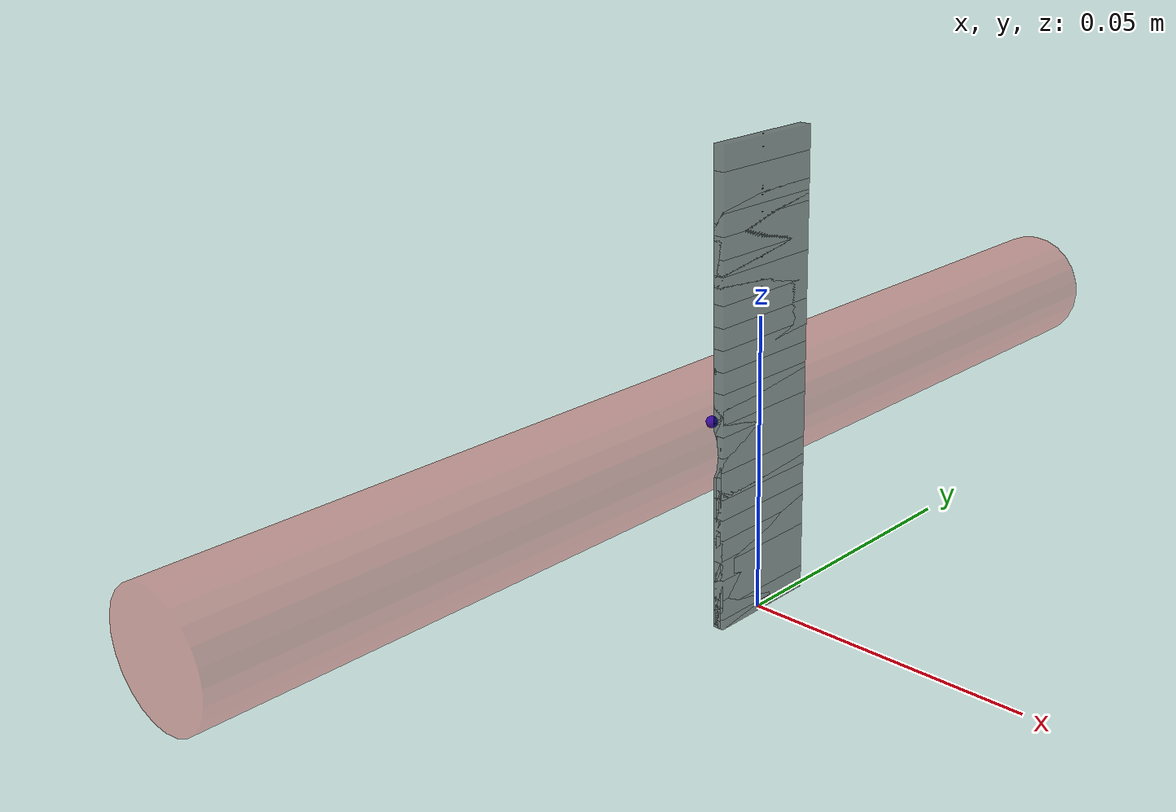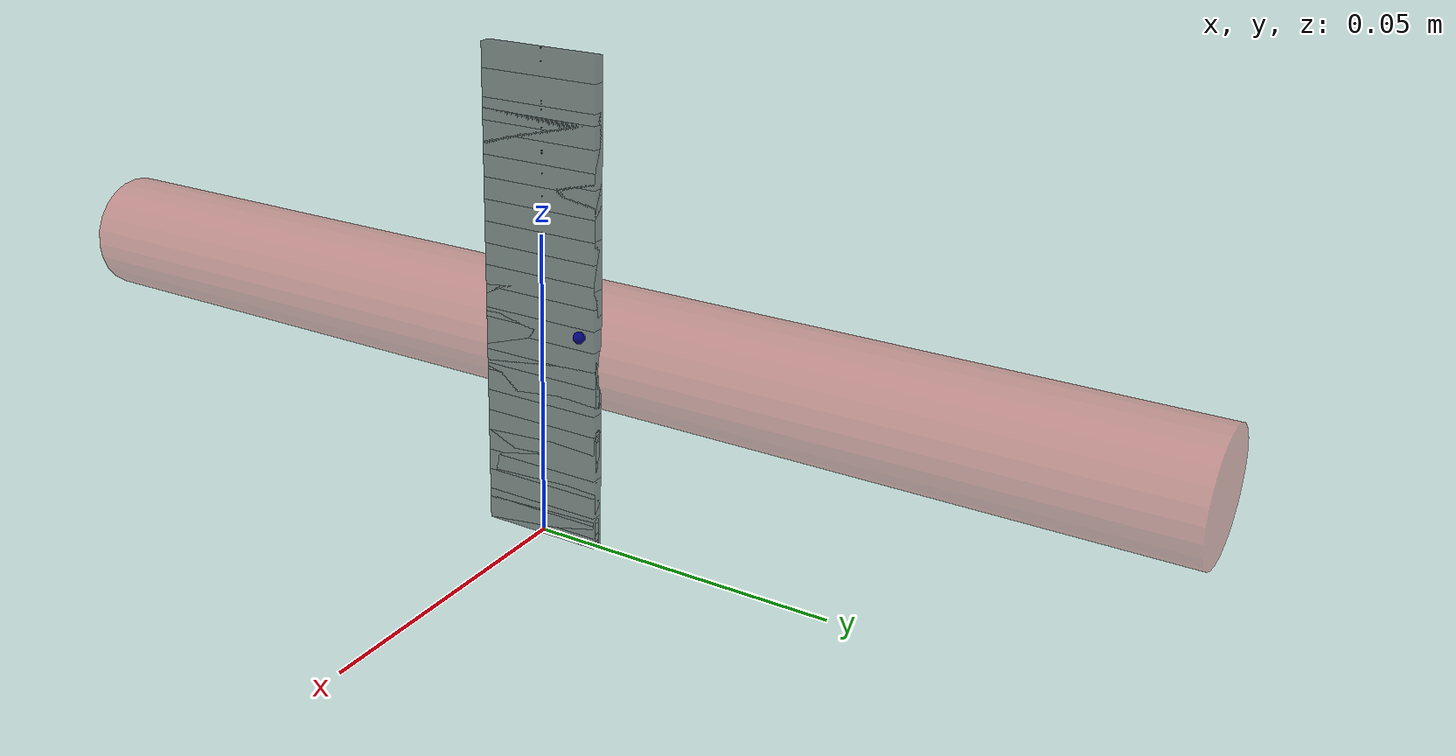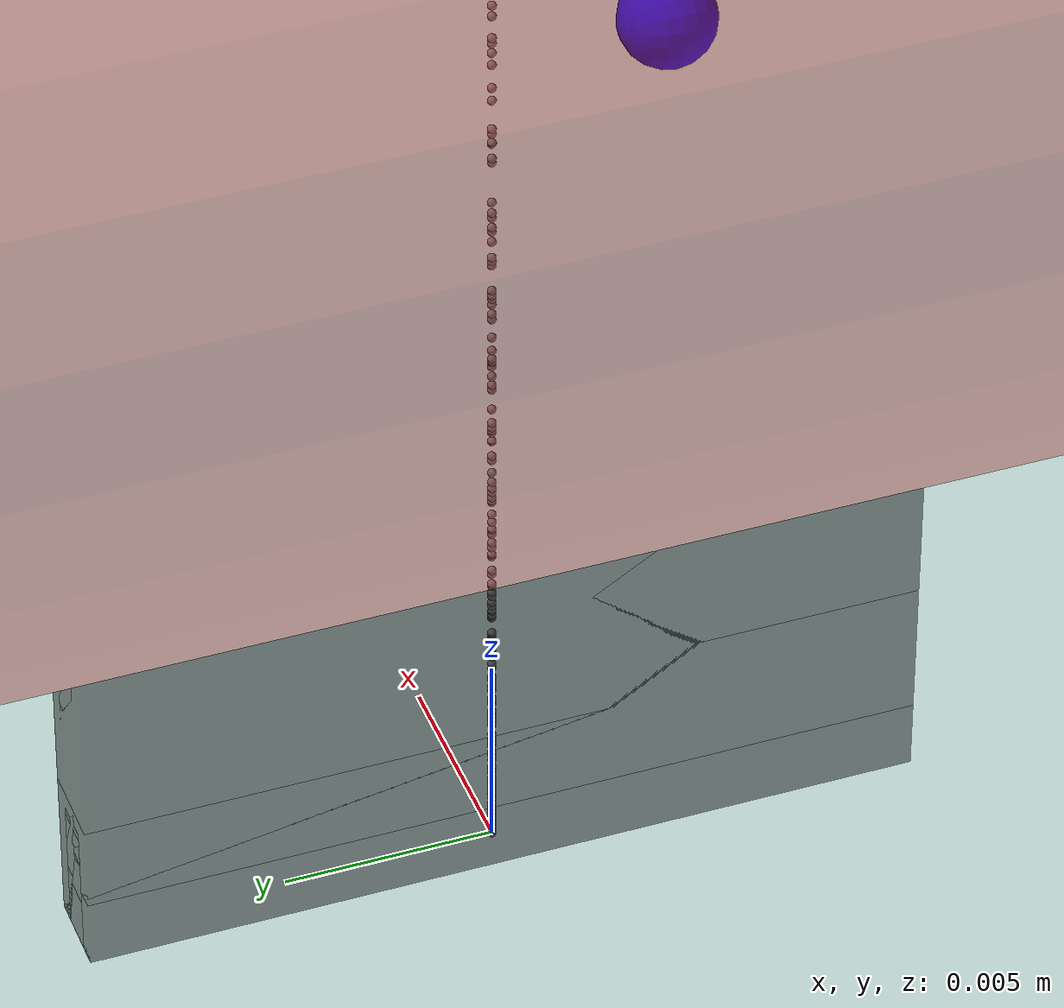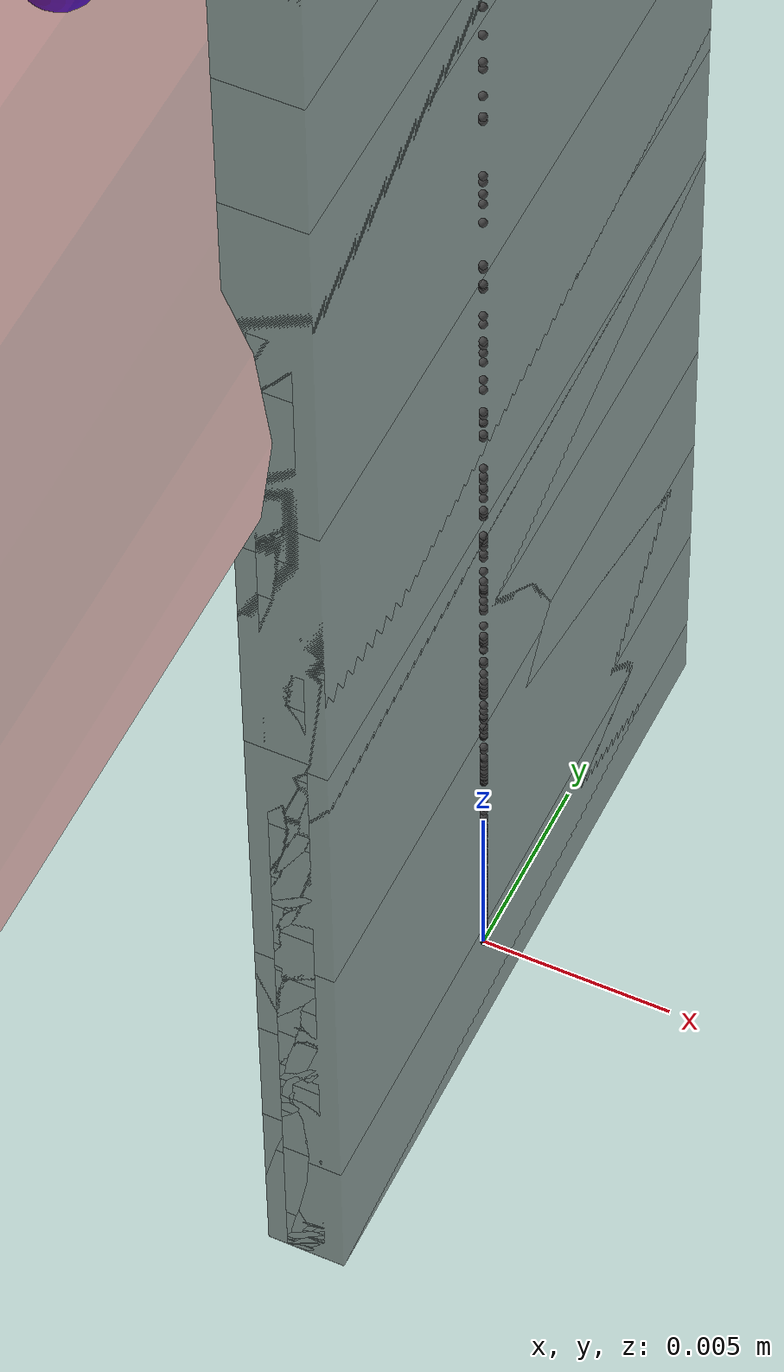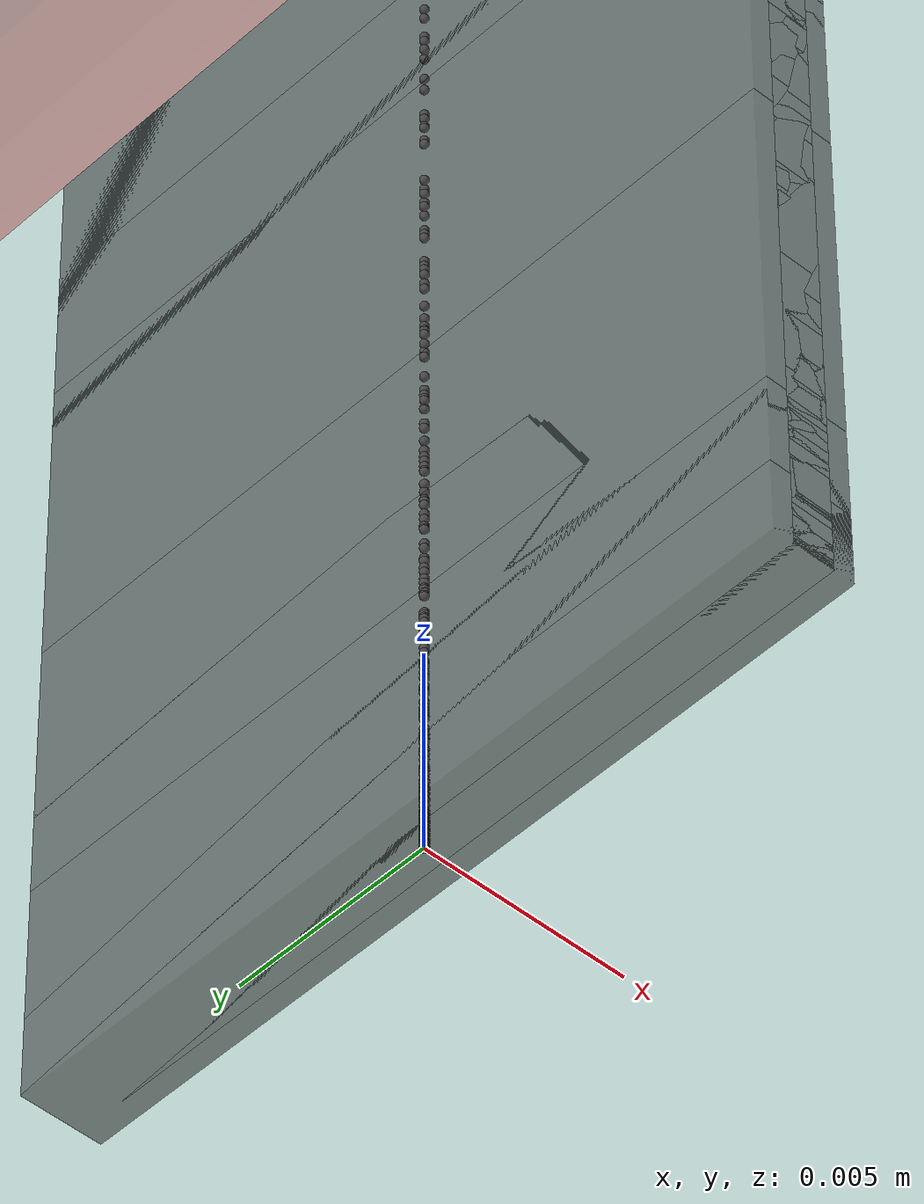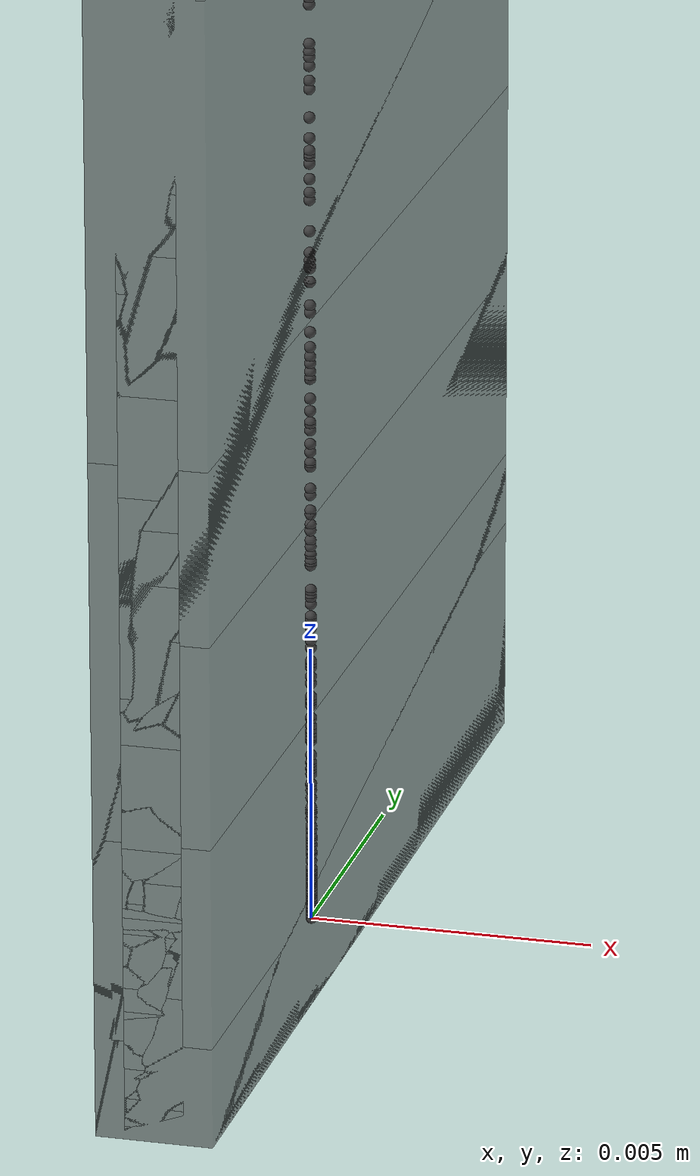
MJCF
<?xml version='1.0' encoding='UTF-8'?>
<mujoco>
    <option timestep="1e-5"/>
    <option gravity="0 0 0"/>
    <option integrator="implicitfast"/>
    <!--Euler, RK4, implicit, implicitfast-->

    <asset>
        <texture type="skybox" builtin="gradient" rgb1="1 1 1" rgb2="0.5 0.5 0.5" width="265" height="256"/>
        <texture name="grid" type="2d" builtin="checker" rgb1="0.1 0.2 0.3" rgb2="0.2 0.3 0.4" width="300" height="300"/>
        <material name="grid" texture="grid" texrepeat="10 10" reflectance="0.2"/>
    </asset>

    <default class="main">
        <geom condim="1" contype="1" conaffinity="0" solref="0.0001 12"/>
        <equality solref="0.0001 12"/>
    </default>

    <worldbody>

    <light pos="0 0 100"/>
    <camera name="side view" pos="0 -0.3 0.025" euler="90 0 0" fovy="20"/>

    <body name="IDF_b_0" pos="0 0 0" euler="0 0 0">
<site name="IDF_b_0_sroot" size="0.0001" pos="0 0 0"/>
<geom name="IDF_b_0_g" type="box" size="0.001 0.01 0.0008750000000000001" pos="0 0 0.0008750000000000001" rgba="0.1 0.1 0.1 0.5"/>
<site name="IDF_b_0_s" size="0.0001" pos="0 0 0.0008750000000000001"/>
<body name="IDF_b_1" pos="0 0 0.0017500000000000003" euler="0 0 0">
<joint name="IDF_b_1_j" type="hinge" axis="0 1 0" pos="0 0 0" stiffness="0.07047619047619047" damping="0.0003523809523809524"/>
<geom name="IDF_b_1_g" type="box" size="0.001 0.01 0.0017500000000000003" pos="0 0 0.0017500000000000003" rgba="0.1 0.1 0.1 0.5"/>
<site name="IDF_b_1_s" size="0.0001" pos="0 0 0.0017500000000000003"/>
<body name="IDF_b_2" pos="0 0 0.0035000000000000005" euler="0 0 0">
<joint name="IDF_b_2_j" type="hinge" axis="0 1 0" pos="0 0 0" stiffness="0.07047619047619047" damping="0.0003523809523809524"/>
<geom name="IDF_b_2_g" type="box" size="0.001 0.01 0.0017500000000000003" pos="0 0 0.0017500000000000003" rgba="0.1 0.1 0.1 0.5"/>
<site name="IDF_b_2_s" size="0.0001" pos="0 0 0.0017500000000000003"/>
<body name="IDF_b_3" pos="0 0 0.0035000000000000005" euler="0 0 0">
<joint name="IDF_b_3_j" type="hinge" axis="0 1 0" pos="0 0 0" stiffness="0.07047619047619047" damping="0.0003523809523809524"/>
<geom name="IDF_b_3_g" type="box" size="0.001 0.01 0.0017500000000000003" pos="0 0 0.0017500000000000003" rgba="0.1 0.1 0.1 0.5"/>
<site name="IDF_b_3_s" size="0.0001" pos="0 0 0.0017500000000000003"/>
<body name="IDF_b_4" pos="0 0 0.0035000000000000005" euler="0 0 0">
<joint name="IDF_b_4_j" type="hinge" axis="0 1 0" pos="0 0 0" stiffness="0.07047619047619047" damping="0.0003523809523809524"/>
<geom name="IDF_b_4_g" type="box" size="0.001 0.01 0.0017500000000000003" pos="0 0 0.0017500000000000003" rgba="0.1 0.1 0.1 0.5"/>
<site name="IDF_b_4_s" size="0.0001" pos="0 0 0.0017500000000000003"/>
<body name="IDF_b_5" pos="0 0 0.0035000000000000005" euler="0 0 0">
<joint name="IDF_b_5_j" type="hinge" axis="0 1 0" pos="0 0 0" stiffness="0.07047619047619047" damping="0.0003523809523809524"/>
<geom name="IDF_b_5_g" type="box" size="0.001 0.01 0.0017500000000000003" pos="0 0 0.0017500000000000003" rgba="0.1 0.1 0.1 0.5"/>
<site name="IDF_b_5_s" size="0.0001" pos="0 0 0.0017500000000000003"/>
<body name="IDF_b_6" pos="0 0 0.0035000000000000005" euler="0 0 0">
<joint name="IDF_b_6_j" type="hinge" axis="0 1 0" pos="0 0 0" stiffness="0.07047619047619047" damping="0.0003523809523809524"/>
<geom name="IDF_b_6_g" type="box" size="0.001 0.01 0.0017500000000000003" pos="0 0 0.0017500000000000003" rgba="0.1 0.1 0.1 0.5"/>
<site name="IDF_b_6_s" size="0.0001" pos="0 0 0.0017500000000000003"/>
<body name="IDF_b_7" pos="0 0 0.0035000000000000005" euler="0 0 0">
<joint name="IDF_b_7_j" type="hinge" axis="0 1 0" pos="0 0 0" stiffness="0.07047619047619047" damping="0.0003523809523809524"/>
<geom name="IDF_b_7_g" type="box" size="0.001 0.01 0.0017500000000000003" pos="0 0 0.0017500000000000003" rgba="0.1 0.1 0.1 0.5"/>
<site name="IDF_b_7_s" size="0.0001" pos="0 0 0.0017500000000000003"/>
<body name="IDF_b_8" pos="0 0 0.0035000000000000005" euler="0 0 0">
<joint name="IDF_b_8_j" type="hinge" axis="0 1 0" pos="0 0 0" stiffness="0.07047619047619047" damping="0.0003523809523809524"/>
<geom name="IDF_b_8_g" type="box" size="0.001 0.01 0.0017500000000000003" pos="0 0 0.0017500000000000003" rgba="0.1 0.1 0.1 0.5"/>
<site name="IDF_b_8_s" size="0.0001" pos="0 0 0.0017500000000000003"/>
<body name="IDF_b_9" pos="0 0 0.0035000000000000005" euler="0 0 0">
<joint name="IDF_b_9_j" type="hinge" axis="0 1 0" pos="0 0 0" stiffness="0.07047619047619047" damping="0.0003523809523809524"/>
<geom name="IDF_b_9_g" type="box" size="0.001 0.01 0.0017500000000000003" pos="0 0 0.0017500000000000003" rgba="0.1 0.1 0.1 0.5"/>
<site name="IDF_b_9_s" size="0.0001" pos="0 0 0.0017500000000000003"/>
<body name="IDF_b_10" pos="0 0 0.0035000000000000005" euler="0 0 0">
<joint name="IDF_b_10_j" type="hinge" axis="0 1 0" pos="0 0 0" stiffness="0.07047619047619047" damping="0.0003523809523809524"/>
<geom name="IDF_b_10_g" type="box" size="0.001 0.01 0.0017500000000000003" pos="0 0 0.0017500000000000003" rgba="0.1 0.1 0.1 0.5"/>
<site name="IDF_b_10_s" size="0.0001" pos="0 0 0.0017500000000000003"/>
<body name="IDF_b_11" pos="0 0 0.0035000000000000005" euler="0 0 0">
<joint name="IDF_b_11_j" type="hinge" axis="0 1 0" pos="0 0 0" stiffness="0.07047619047619047" damping="0.0003523809523809524"/>
<geom name="IDF_b_11_g" type="box" size="0.001 0.01 0.0017500000000000003" pos="0 0 0.0017500000000000003" rgba="0.1 0.1 0.1 0.5"/>
<site name="IDF_b_11_s" size="0.0001" pos="0 0 0.0017500000000000003"/>
<body name="IDF_b_12" pos="0 0 0.0035000000000000005" euler="0 0 0">
<joint name="IDF_b_12_j" type="hinge" axis="0 1 0" pos="0 0 0" stiffness="0.07047619047619047" damping="0.0003523809523809524"/>
<geom name="IDF_b_12_g" type="box" size="0.001 0.01 0.0017500000000000003" pos="0 0 0.0017500000000000003" rgba="0.1 0.1 0.1 0.5"/>
<site name="IDF_b_12_s" size="0.0001" pos="0 0 0.0017500000000000003"/>
<body name="IDF_b_13" pos="0 0 0.0035000000000000005" euler="0 0 0">
<joint name="IDF_b_13_j" type="hinge" axis="0 1 0" pos="0 0 0" stiffness="0.07047619047619047" damping="0.0003523809523809524"/>
<geom name="IDF_b_13_g" type="box" size="0.001 0.01 0.0017500000000000003" pos="0 0 0.0017500000000000003" rgba="0.1 0.1 0.1 0.5"/>
<site name="IDF_b_13_s" size="0.0001" pos="0 0 0.0017500000000000003"/>
<body name="IDF_b_14" pos="0 0 0.0035000000000000005" euler="0 0 0">
<joint name="IDF_b_14_j" type="hinge" axis="0 1 0" pos="0 0 0" stiffness="0.07047619047619047" damping="0.0003523809523809524"/>
<geom name="IDF_b_14_g" type="box" size="0.001 0.01 0.0017500000000000003" pos="0 0 0.0017500000000000003" rgba="0.1 0.1 0.1 0.5"/>
<site name="IDF_b_14_s" size="0.0001" pos="0 0 0.0017500000000000003"/>
<body name="IDF_b_15" pos="0 0 0.0035000000000000005" euler="0 0 0">
<joint name="IDF_b_15_j" type="hinge" axis="0 1 0" pos="0 0 0" stiffness="0.07047619047619047" damping="0.0003523809523809524"/>
<geom name="IDF_b_15_g" type="box" size="0.001 0.01 0.0017500000000000003" pos="0 0 0.0017500000000000003" rgba="0.1 0.1 0.1 0.5"/>
<site name="IDF_b_15_s" size="0.0001" pos="0 0 0.0017500000000000003"/>
<body name="IDF_b_16" pos="0 0 0.0035000000000000005" euler="0 0 0">
<joint name="IDF_b_16_j" type="hinge" axis="0 1 0" pos="0 0 0" stiffness="0.07047619047619047" damping="0.0003523809523809524"/>
<geom name="IDF_b_16_g" type="box" size="0.001 0.01 0.0017500000000000003" pos="0 0 0.0017500000000000003" rgba="0.1 0.1 0.1 0.5"/>
<site name="IDF_b_16_s" size="0.0001" pos="0 0 0.0017500000000000003"/>
<body name="IDF_b_17" pos="0 0 0.0035000000000000005" euler="0 0 0">
<joint name="IDF_b_17_j" type="hinge" axis="0 1 0" pos="0 0 0" stiffness="0.07047619047619047" damping="0.0003523809523809524"/>
<geom name="IDF_b_17_g" type="box" size="0.001 0.01 0.0017500000000000003" pos="0 0 0.0017500000000000003" rgba="0.1 0.1 0.1 0.5"/>
<site name="IDF_b_17_s" size="0.0001" pos="0 0 0.0017500000000000003"/>
<body name="IDF_b_18" pos="0 0 0.0035000000000000005" euler="0 0 0">
<joint name="IDF_b_18_j" type="hinge" axis="0 1 0" pos="0 0 0" stiffness="0.07047619047619047" damping="0.0003523809523809524"/>
<geom name="IDF_b_18_g" type="box" size="0.001 0.01 0.0017500000000000003" pos="0 0 0.0017500000000000003" rgba="0.1 0.1 0.1 0.5"/>
<site name="IDF_b_18_s" size="0.0001" pos="0 0 0.0017500000000000003"/>
<body name="IDF_b_19" pos="0 0 0.0035000000000000005" euler="0 0 0">
<joint name="IDF_b_19_j" type="hinge" axis="0 1 0" pos="0 0 0" stiffness="0.07047619047619047" damping="0.0003523809523809524"/>
<geom name="IDF_b_19_g" type="box" size="0.001 0.01 0.0017500000000000003" pos="0 0 0.0017500000000000003" rgba="0.1 0.1 0.1 0.5"/>
<site name="IDF_b_19_s" size="0.0001" pos="0 0 0.0017500000000000003"/>
<body name="IDF_b_20" pos="0 0 0.0035000000000000005" euler="0 0 0">
<joint name="IDF_b_20_j" type="hinge" axis="0 1 0" pos="0 0 0" stiffness="0.07047619047619047" damping="0.0003523809523809524"/>
<geom name="IDF_b_20_g" type="box" size="0.001 0.01 0.0008750000000000001" pos="0 0 0.0008750000000000001" rgba="0.1 0.1 0.1 0.5"/>
<site name="IDF_b_20_s" size="0.0001" pos="0 0 0.0008750000000000001"/>
<site name="IDF_b_21_s" size="0.0001" pos="0 0 0.0017500000000000003"/>
</body>
</body>
</body>
</body>
</body>
</body>
</body>
</body>
</body>
</body>
</body>
</body>
</body>
</body>
</body>
</body>
</body>
</body>
</body>
</body>
</body><body name="IDB_b_0" pos="0 0 0" euler="0 0 0">
<site name="IDB_b_0_sroot" size="0.0001" pos="0 0 0"/>
<geom name="IDB_b_0_g" type="box" size="0.001 0.01 0.001956559480312316" pos="0 0 0.001956559480312316" rgba="0.1 0.1 0.1 0.5"/>
<site name="IDB_b_0_s" size="0.0001" pos="0 0 0.001956559480312316"/>
<body name="IDB_b_1" pos="0 0 0.003913118960624632" euler="0 0 0">
<joint name="IDB_b_1_j" type="hinge" axis="0 1 0" pos="0 0 0" stiffness="0.031517910539997036" damping="0.0001575895526999852"/>
<geom name="IDB_b_1_g" type="box" size="0.001 0.01 0.003913118960624632" pos="0 0 0.003913118960624632" rgba="0.1 0.1 0.1 0.5"/>
<site name="IDB_b_1_s" size="0.0001" pos="0 0 0.003913118960624632"/>
<body name="IDB_b_2" pos="0 0 0.007826237921249264" euler="0 0 0">
<joint name="IDB_b_2_j" type="hinge" axis="0 1 0" pos="0 0 0" stiffness="0.031517910539997036" damping="0.0001575895526999852"/>
<geom name="IDB_b_2_g" type="box" size="0.001 0.01 0.003913118960624632" pos="0 0 0.003913118960624632" rgba="0.1 0.1 0.1 0.5"/>
<site name="IDB_b_2_s" size="0.0001" pos="0 0 0.003913118960624632"/>
<body name="IDB_b_3" pos="0 0 0.007826237921249264" euler="0 0 0">
<joint name="IDB_b_3_j" type="hinge" axis="0 1 0" pos="0 0 0" stiffness="0.031517910539997036" damping="0.0001575895526999852"/>
<geom name="IDB_b_3_g" type="box" size="0.001 0.01 0.003913118960624632" pos="0 0 0.003913118960624632" rgba="0.1 0.1 0.1 0.5"/>
<site name="IDB_b_3_s" size="0.0001" pos="0 0 0.003913118960624632"/>
<body name="IDB_b_4" pos="0 0 0.007826237921249264" euler="0 0 0">
<joint name="IDB_b_4_j" type="hinge" axis="0 1 0" pos="0 0 0" stiffness="0.031517910539997036" damping="0.0001575895526999852"/>
<geom name="IDB_b_4_g" type="box" size="0.001 0.01 0.003913118960624632" pos="0 0 0.003913118960624632" rgba="0.1 0.1 0.1 0.5"/>
<site name="IDB_b_4_s" size="0.0001" pos="0 0 0.003913118960624632"/>
<body name="IDB_b_5" pos="0 0 0.007826237921249264" euler="0 0 0">
<joint name="IDB_b_5_j" type="hinge" axis="0 1 0" pos="0 0 0" stiffness="0.031517910539997036" damping="0.0001575895526999852"/>
<geom name="IDB_b_5_g" type="box" size="0.001 0.01 0.003913118960624632" pos="0 0 0.003913118960624632" rgba="0.1 0.1 0.1 0.5"/>
<site name="IDB_b_5_s" size="0.0001" pos="0 0 0.003913118960624632"/>
<body name="IDB_b_6" pos="0 0 0.007826237921249264" euler="0 0 0">
<joint name="IDB_b_6_j" type="hinge" axis="0 1 0" pos="0 0 0" stiffness="0.031517910539997036" damping="0.0001575895526999852"/>
<geom name="IDB_b_6_g" type="box" size="0.001 0.01 0.003913118960624632" pos="0 0 0.003913118960624632" rgba="0.1 0.1 0.1 0.5"/>
<site name="IDB_b_6_s" size="0.0001" pos="0 0 0.003913118960624632"/>
<body name="IDB_b_7" pos="0 0 0.007826237921249264" euler="0 0 0">
<joint name="IDB_b_7_j" type="hinge" axis="0 1 0" pos="0 0 0" stiffness="0.031517910539997036" damping="0.0001575895526999852"/>
<geom name="IDB_b_7_g" type="box" size="0.001 0.01 0.003913118960624632" pos="0 0 0.003913118960624632" rgba="0.1 0.1 0.1 0.5"/>
<site name="IDB_b_7_s" size="0.0001" pos="0 0 0.003913118960624632"/>
<body name="IDB_b_8" pos="0 0 0.007826237921249264" euler="0 0 0">
<joint name="IDB_b_8_j" type="hinge" axis="0 1 0" pos="0 0 0" stiffness="0.031517910539997036" damping="0.0001575895526999852"/>
<geom name="IDB_b_8_g" type="box" size="0.001 0.01 0.003913118960624632" pos="0 0 0.003913118960624632" rgba="0.1 0.1 0.1 0.5"/>
<site name="IDB_b_8_s" size="0.0001" pos="0 0 0.003913118960624632"/>
<body name="IDB_b_9" pos="0 0 0.007826237921249264" euler="0 0 0">
<joint name="IDB_b_9_j" type="hinge" axis="0 1 0" pos="0 0 0" stiffness="0.031517910539997036" damping="0.0001575895526999852"/>
<geom name="IDB_b_9_g" type="box" size="0.001 0.01 0.003913118960624632" pos="0 0 0.003913118960624632" rgba="0.1 0.1 0.1 0.5"/>
<site name="IDB_b_9_s" size="0.0001" pos="0 0 0.003913118960624632"/>
<body name="IDB_b_10" pos="0 0 0.007826237921249264" euler="0 0 0">
<joint name="IDB_b_10_j" type="hinge" axis="0 1 0" pos="0 0 0" stiffness="0.031517910539997036" damping="0.0001575895526999852"/>
<geom name="IDB_b_10_g" type="box" size="0.001 0.01 0.001956559480312316" pos="0 0 0.001956559480312316" rgba="0.1 0.1 0.1 0.5"/>
<site name="IDB_b_10_s" size="0.0001" pos="0 0 0.001956559480312316"/>
<site name="IDB_b_11_s" size="0.0001" pos="0 0 0.003913118960624632"/>
</body>
</body>
</body>
</body>
</body>
</body>
</body>
</body>
</body>
</body>
</body><body>
<joint type="free"/>
<body name="IDR596_b_0" pos="0 0 0" euler="0 0 0">
<site name="IDR596_b_0_sroot" size="0.0001" pos="0 0 0"/>
<geom name="IDR596_b_0_g" type="box" size="0.0005 0.01 0.0008286933447401586" pos="0 0 0.0008286933447401586" rgba="0.1 0.1 0.1 0.5"/>
<site name="IDR596_b_0_s" size="0.0001" pos="0 0 0.0008286933447401586"/>
<body name="IDR596_b_1" pos="0 0 0.0016573866894803173" euler="0 0 0">
<joint name="IDR596_b_1_j" type="hinge" axis="0 1 0" pos="0 0 0" stiffness="0.009301792251934067" damping="4.6508961259670335e-05"/>
<geom name="IDR596_b_1_g" type="box" size="0.0005 0.01 0.0016573866894803173" pos="0 0 0.0016573866894803173" rgba="0.1 0.1 0.1 0.5"/>
<site name="IDR596_b_1_s" size="0.0001" pos="0 0 0.0016573866894803173"/>
<body name="IDR596_b_2" pos="0 0 0.0033147733789606346" euler="0 0 0">
<joint name="IDR596_b_2_j" type="hinge" axis="0 1 0" pos="0 0 0" stiffness="0.009301792251934067" damping="4.6508961259670335e-05"/>
<geom name="IDR596_b_2_g" type="box" size="0.0005 0.01 0.0016573866894803173" pos="0 0 0.0016573866894803173" rgba="0.1 0.1 0.1 0.5"/>
<site name="IDR596_b_2_s" size="0.0001" pos="0 0 0.0016573866894803173"/>
<body name="IDR596_b_3" pos="0 0 0.0033147733789606346" euler="0 0 0">
<joint name="IDR596_b_3_j" type="hinge" axis="0 1 0" pos="0 0 0" stiffness="0.009301792251934067" damping="4.6508961259670335e-05"/>
<geom name="IDR596_b_3_g" type="box" size="0.0005 0.01 0.0016573866894803173" pos="0 0 0.0016573866894803173" rgba="0.1 0.1 0.1 0.5"/>
<site name="IDR596_b_3_s" size="0.0001" pos="0 0 0.0016573866894803173"/>
<body name="IDR596_b_4" pos="0 0 0.0033147733789606346" euler="0 0 0">
<joint name="IDR596_b_4_j" type="hinge" axis="0 1 0" pos="0 0 0" stiffness="0.009301792251934067" damping="4.6508961259670335e-05"/>
<geom name="IDR596_b_4_g" type="box" size="0.0005 0.01 0.0016573866894803173" pos="0 0 0.0016573866894803173" rgba="0.1 0.1 0.1 0.5"/>
<site name="IDR596_b_4_s" size="0.0001" pos="0 0 0.0016573866894803173"/>
<body name="IDR596_b_5" pos="0 0 0.0033147733789606346" euler="0 0 0">
<joint name="IDR596_b_5_j" type="hinge" axis="0 1 0" pos="0 0 0" stiffness="0.009301792251934067" damping="4.6508961259670335e-05"/>
<geom name="IDR596_b_5_g" type="box" size="0.0005 0.01 0.0016573866894803173" pos="0 0 0.0016573866894803173" rgba="0.1 0.1 0.1 0.5"/>
<site name="IDR596_b_5_s" size="0.0001" pos="0 0 0.0016573866894803173"/>
<body name="IDR596_b_6" pos="0 0 0.0033147733789606346" euler="0 0 0">
<joint name="IDR596_b_6_j" type="hinge" axis="0 1 0" pos="0 0 0" stiffness="0.009301792251934067" damping="4.6508961259670335e-05"/>
<geom name="IDR596_b_6_g" type="box" size="0.0005 0.01 0.0016573866894803173" pos="0 0 0.0016573866894803173" rgba="0.1 0.1 0.1 0.5"/>
<site name="IDR596_b_6_s" size="0.0001" pos="0 0 0.0016573866894803173"/>
<body name="IDR596_b_7" pos="0 0 0.0033147733789606346" euler="0 0 0">
<joint name="IDR596_b_7_j" type="hinge" axis="0 1 0" pos="0 0 0" stiffness="0.009301792251934067" damping="4.6508961259670335e-05"/>
<geom name="IDR596_b_7_g" type="box" size="0.0005 0.01 0.0016573866894803173" pos="0 0 0.0016573866894803173" rgba="0.1 0.1 0.1 0.5"/>
<site name="IDR596_b_7_s" size="0.0001" pos="0 0 0.0016573866894803173"/>
<body name="IDR596_b_8" pos="0 0 0.0033147733789606346" euler="0 0 0">
<joint name="IDR596_b_8_j" type="hinge" axis="0 1 0" pos="0 0 0" stiffness="0.009301792251934067" damping="4.6508961259670335e-05"/>
<geom name="IDR596_b_8_g" type="box" size="0.0005 0.01 0.0016573866894803173" pos="0 0 0.0016573866894803173" rgba="0.1 0.1 0.1 0.5"/>
<site name="IDR596_b_8_s" size="0.0001" pos="0 0 0.0016573866894803173"/>
<body name="IDR596_b_9" pos="0 0 0.0033147733789606346" euler="0 0 0">
<joint name="IDR596_b_9_j" type="hinge" axis="0 1 0" pos="0 0 0" stiffness="0.009301792251934067" damping="4.6508961259670335e-05"/>
<geom name="IDR596_b_9_g" type="box" size="0.0005 0.01 0.0016573866894803173" pos="0 0 0.0016573866894803173" rgba="0.1 0.1 0.1 0.5"/>
<site name="IDR596_b_9_s" size="0.0001" pos="0 0 0.0016573866894803173"/>
<body name="IDR596_b_10" pos="0 0 0.0033147733789606346" euler="0 0 0">
<joint name="IDR596_b_10_j" type="hinge" axis="0 1 0" pos="0 0 0" stiffness="0.009301792251934067" damping="4.6508961259670335e-05"/>
<geom name="IDR596_b_10_g" type="box" size="0.0005 0.01 0.0008286933447401586" pos="0 0 0.0008286933447401586" rgba="0.1 0.1 0.1 0.5"/>
<site name="IDR596_b_10_s" size="0.0001" pos="0 0 0.0008286933447401586"/>
<site name="IDR596_b_11_s" size="0.0001" pos="0 0 0.0016573866894803173"/>
</body>
</body>
</body>
</body>
</body>
</body>
</body>
</body>
</body>
</body>
</body>
</body><body>
<joint type="free"/>
<body name="IDR597_b_0" pos="0 0 0" euler="0 0 0">
<site name="IDR597_b_0_sroot" size="0.0001" pos="0 0 0"/>
<geom name="IDR597_b_0_g" type="box" size="0.0005 0.01 0.0007618688974596652" pos="0 0 0.0007618688974596652" rgba="0.1 0.1 0.1 0.5"/>
<site name="IDR597_b_0_s" size="0.0001" pos="0 0 0.0007618688974596652"/>
<body name="IDR597_b_1" pos="0 0 0.0015237377949193305" euler="0 0 0">
<joint name="IDR597_b_1_j" type="hinge" axis="0 1 0" pos="0 0 0" stiffness="0.010117663759520288" damping="5.058831879760144e-05"/>
<geom name="IDR597_b_1_g" type="box" size="0.0005 0.01 0.0015237377949193305" pos="0 0 0.0015237377949193305" rgba="0.1 0.1 0.1 0.5"/>
<site name="IDR597_b_1_s" size="0.0001" pos="0 0 0.0015237377949193305"/>
<body name="IDR597_b_2" pos="0 0 0.003047475589838661" euler="0 0 0">
<joint name="IDR597_b_2_j" type="hinge" axis="0 1 0" pos="0 0 0" stiffness="0.010117663759520288" damping="5.058831879760144e-05"/>
<geom name="IDR597_b_2_g" type="box" size="0.0005 0.01 0.0015237377949193305" pos="0 0 0.0015237377949193305" rgba="0.1 0.1 0.1 0.5"/>
<site name="IDR597_b_2_s" size="0.0001" pos="0 0 0.0015237377949193305"/>
<body name="IDR597_b_3" pos="0 0 0.003047475589838661" euler="0 0 0">
<joint name="IDR597_b_3_j" type="hinge" axis="0 1 0" pos="0 0 0" stiffness="0.010117663759520288" damping="5.058831879760144e-05"/>
<geom name="IDR597_b_3_g" type="box" size="0.0005 0.01 0.0015237377949193305" pos="0 0 0.0015237377949193305" rgba="0.1 0.1 0.1 0.5"/>
<site name="IDR597_b_3_s" size="0.0001" pos="0 0 0.0015237377949193305"/>
<body name="IDR597_b_4" pos="0 0 0.003047475589838661" euler="0 0 0">
<joint name="IDR597_b_4_j" type="hinge" axis="0 1 0" pos="0 0 0" stiffness="0.010117663759520288" damping="5.058831879760144e-05"/>
<geom name="IDR597_b_4_g" type="box" size="0.0005 0.01 0.0015237377949193305" pos="0 0 0.0015237377949193305" rgba="0.1 0.1 0.1 0.5"/>
<site name="IDR597_b_4_s" size="0.0001" pos="0 0 0.0015237377949193305"/>
<body name="IDR597_b_5" pos="0 0 0.003047475589838661" euler="0 0 0">
<joint name="IDR597_b_5_j" type="hinge" axis="0 1 0" pos="0 0 0" stiffness="0.010117663759520288" damping="5.058831879760144e-05"/>
<geom name="IDR597_b_5_g" type="box" size="0.0005 0.01 0.0015237377949193305" pos="0 0 0.0015237377949193305" rgba="0.1 0.1 0.1 0.5"/>
<site name="IDR597_b_5_s" size="0.0001" pos="0 0 0.0015237377949193305"/>
<body name="IDR597_b_6" pos="0 0 0.003047475589838661" euler="0 0 0">
<joint name="IDR597_b_6_j" type="hinge" axis="0 1 0" pos="0 0 0" stiffness="0.010117663759520288" damping="5.058831879760144e-05"/>
<geom name="IDR597_b_6_g" type="box" size="0.0005 0.01 0.0015237377949193305" pos="0 0 0.0015237377949193305" rgba="0.1 0.1 0.1 0.5"/>
<site name="IDR597_b_6_s" size="0.0001" pos="0 0 0.0015237377949193305"/>
<body name="IDR597_b_7" pos="0 0 0.003047475589838661" euler="0 0 0">
<joint name="IDR597_b_7_j" type="hinge" axis="0 1 0" pos="0 0 0" stiffness="0.010117663759520288" damping="5.058831879760144e-05"/>
<geom name="IDR597_b_7_g" type="box" size="0.0005 0.01 0.0015237377949193305" pos="0 0 0.0015237377949193305" rgba="0.1 0.1 0.1 0.5"/>
<site name="IDR597_b_7_s" size="0.0001" pos="0 0 0.0015237377949193305"/>
<body name="IDR597_b_8" pos="0 0 0.003047475589838661" euler="0 0 0">
<joint name="IDR597_b_8_j" type="hinge" axis="0 1 0" pos="0 0 0" stiffness="0.010117663759520288" damping="5.058831879760144e-05"/>
<geom name="IDR597_b_8_g" type="box" size="0.0005 0.01 0.0015237377949193305" pos="0 0 0.0015237377949193305" rgba="0.1 0.1 0.1 0.5"/>
<site name="IDR597_b_8_s" size="0.0001" pos="0 0 0.0015237377949193305"/>
<body name="IDR597_b_9" pos="0 0 0.003047475589838661" euler="0 0 0">
<joint name="IDR597_b_9_j" type="hinge" axis="0 1 0" pos="0 0 0" stiffness="0.010117663759520288" damping="5.058831879760144e-05"/>
<geom name="IDR597_b_9_g" type="box" size="0.0005 0.01 0.0015237377949193305" pos="0 0 0.0015237377949193305" rgba="0.1 0.1 0.1 0.5"/>
<site name="IDR597_b_9_s" size="0.0001" pos="0 0 0.0015237377949193305"/>
<body name="IDR597_b_10" pos="0 0 0.003047475589838661" euler="0 0 0">
<joint name="IDR597_b_10_j" type="hinge" axis="0 1 0" pos="0 0 0" stiffness="0.010117663759520288" damping="5.058831879760144e-05"/>
<geom name="IDR597_b_10_g" type="box" size="0.0005 0.01 0.0007618688974596652" pos="0 0 0.0007618688974596652" rgba="0.1 0.1 0.1 0.5"/>
<site name="IDR597_b_10_s" size="0.0001" pos="0 0 0.0007618688974596652"/>
<site name="IDR597_b_11_s" size="0.0001" pos="0 0 0.0015237377949193305"/>
</body>
</body>
</body>
</body>
</body>
</body>
</body>
</body>
</body>
</body>
</body>
</body><body>
<joint type="free"/>
<body name="IDR598_b_0" pos="0 0 0" euler="0 0 0">
<site name="IDR598_b_0_sroot" size="0.0001" pos="0 0 0"/>
<geom name="IDR598_b_0_g" type="box" size="0.0005 0.01 0.000695230521120507" pos="0 0 0.000695230521120507" rgba="0.1 0.1 0.1 0.5"/>
<site name="IDR598_b_0_s" size="0.0001" pos="0 0 0.000695230521120507"/>
<body name="IDR598_b_1" pos="0 0 0.001390461042241014" euler="0 0 0">
<joint name="IDR598_b_1_j" type="hinge" axis="0 1 0" pos="0 0 0" stiffness="0.011087449556889086" damping="5.543724778444543e-05"/>
<geom name="IDR598_b_1_g" type="box" size="0.0005 0.01 0.001390461042241014" pos="0 0 0.001390461042241014" rgba="0.1 0.1 0.1 0.5"/>
<site name="IDR598_b_1_s" size="0.0001" pos="0 0 0.001390461042241014"/>
<body name="IDR598_b_2" pos="0 0 0.002780922084482028" euler="0 0 0">
<joint name="IDR598_b_2_j" type="hinge" axis="0 1 0" pos="0 0 0" stiffness="0.011087449556889086" damping="5.543724778444543e-05"/>
<geom name="IDR598_b_2_g" type="box" size="0.0005 0.01 0.001390461042241014" pos="0 0 0.001390461042241014" rgba="0.1 0.1 0.1 0.5"/>
<site name="IDR598_b_2_s" size="0.0001" pos="0 0 0.001390461042241014"/>
<body name="IDR598_b_3" pos="0 0 0.002780922084482028" euler="0 0 0">
<joint name="IDR598_b_3_j" type="hinge" axis="0 1 0" pos="0 0 0" stiffness="0.011087449556889086" damping="5.543724778444543e-05"/>
<geom name="IDR598_b_3_g" type="box" size="0.0005 0.01 0.001390461042241014" pos="0 0 0.001390461042241014" rgba="0.1 0.1 0.1 0.5"/>
<site name="IDR598_b_3_s" size="0.0001" pos="0 0 0.001390461042241014"/>
<body name="IDR598_b_4" pos="0 0 0.002780922084482028" euler="0 0 0">
<joint name="IDR598_b_4_j" type="hinge" axis="0 1 0" pos="0 0 0" stiffness="0.011087449556889086" damping="5.543724778444543e-05"/>
<geom name="IDR598_b_4_g" type="box" size="0.0005 0.01 0.001390461042241014" pos="0 0 0.001390461042241014" rgba="0.1 0.1 0.1 0.5"/>
<site name="IDR598_b_4_s" size="0.0001" pos="0 0 0.001390461042241014"/>
<body name="IDR598_b_5" pos="0 0 0.002780922084482028" euler="0 0 0">
<joint name="IDR598_b_5_j" type="hinge" axis="0 1 0" pos="0 0 0" stiffness="0.011087449556889086" damping="5.543724778444543e-05"/>
<geom name="IDR598_b_5_g" type="box" size="0.0005 0.01 0.001390461042241014" pos="0 0 0.001390461042241014" rgba="0.1 0.1 0.1 0.5"/>
<site name="IDR598_b_5_s" size="0.0001" pos="0 0 0.001390461042241014"/>
<body name="IDR598_b_6" pos="0 0 0.002780922084482028" euler="0 0 0">
<joint name="IDR598_b_6_j" type="hinge" axis="0 1 0" pos="0 0 0" stiffness="0.011087449556889086" damping="5.543724778444543e-05"/>
<geom name="IDR598_b_6_g" type="box" size="0.0005 0.01 0.001390461042241014" pos="0 0 0.001390461042241014" rgba="0.1 0.1 0.1 0.5"/>
<site name="IDR598_b_6_s" size="0.0001" pos="0 0 0.001390461042241014"/>
<body name="IDR598_b_7" pos="0 0 0.002780922084482028" euler="0 0 0">
<joint name="IDR598_b_7_j" type="hinge" axis="0 1 0" pos="0 0 0" stiffness="0.011087449556889086" damping="5.543724778444543e-05"/>
<geom name="IDR598_b_7_g" type="box" size="0.0005 0.01 0.001390461042241014" pos="0 0 0.001390461042241014" rgba="0.1 0.1 0.1 0.5"/>
<site name="IDR598_b_7_s" size="0.0001" pos="0 0 0.001390461042241014"/>
<body name="IDR598_b_8" pos="0 0 0.002780922084482028" euler="0 0 0">
<joint name="IDR598_b_8_j" type="hinge" axis="0 1 0" pos="0 0 0" stiffness="0.011087449556889086" damping="5.543724778444543e-05"/>
<geom name="IDR598_b_8_g" type="box" size="0.0005 0.01 0.001390461042241014" pos="0 0 0.001390461042241014" rgba="0.1 0.1 0.1 0.5"/>
<site name="IDR598_b_8_s" size="0.0001" pos="0 0 0.001390461042241014"/>
<body name="IDR598_b_9" pos="0 0 0.002780922084482028" euler="0 0 0">
<joint name="IDR598_b_9_j" type="hinge" axis="0 1 0" pos="0 0 0" stiffness="0.011087449556889086" damping="5.543724778444543e-05"/>
<geom name="IDR598_b_9_g" type="box" size="0.0005 0.01 0.001390461042241014" pos="0 0 0.001390461042241014" rgba="0.1 0.1 0.1 0.5"/>
<site name="IDR598_b_9_s" size="0.0001" pos="0 0 0.001390461042241014"/>
<body name="IDR598_b_10" pos="0 0 0.002780922084482028" euler="0 0 0">
<joint name="IDR598_b_10_j" type="hinge" axis="0 1 0" pos="0 0 0" stiffness="0.011087449556889086" damping="5.543724778444543e-05"/>
<geom name="IDR598_b_10_g" type="box" size="0.0005 0.01 0.000695230521120507" pos="0 0 0.000695230521120507" rgba="0.1 0.1 0.1 0.5"/>
<site name="IDR598_b_10_s" size="0.0001" pos="0 0 0.000695230521120507"/>
<site name="IDR598_b_11_s" size="0.0001" pos="0 0 0.001390461042241014"/>
</body>
</body>
</body>
</body>
</body>
</body>
</body>
</body>
</body>
</body>
</body>
</body><body>
<joint type="free"/>
<body name="IDR599_b_0" pos="0 0 0" euler="0 0 0">
<site name="IDR599_b_0_sroot" size="0.0001" pos="0 0 0"/>
<geom name="IDR599_b_0_g" type="box" size="0.0005 0.01 0.0006287752151466236" pos="0 0 0.0006287752151466236" rgba="0.1 0.1 0.1 0.5"/>
<site name="IDR599_b_0_s" size="0.0001" pos="0 0 0.0006287752151466236"/>
<body name="IDR599_b_1" pos="0 0 0.0012575504302932473" euler="0 0 0">
<joint name="IDR599_b_1_j" type="hinge" axis="0 1 0" pos="0 0 0" stiffness="0.012259283043680139" damping="6.12964152184007e-05"/>
<geom name="IDR599_b_1_g" type="box" size="0.0005 0.01 0.0012575504302932473" pos="0 0 0.0012575504302932473" rgba="0.1 0.1 0.1 0.5"/>
<site name="IDR599_b_1_s" size="0.0001" pos="0 0 0.0012575504302932473"/>
<body name="IDR599_b_2" pos="0 0 0.0025151008605864946" euler="0 0 0">
<joint name="IDR599_b_2_j" type="hinge" axis="0 1 0" pos="0 0 0" stiffness="0.012259283043680139" damping="6.12964152184007e-05"/>
<geom name="IDR599_b_2_g" type="box" size="0.0005 0.01 0.0012575504302932473" pos="0 0 0.0012575504302932473" rgba="0.1 0.1 0.1 0.5"/>
<site name="IDR599_b_2_s" size="0.0001" pos="0 0 0.0012575504302932473"/>
<body name="IDR599_b_3" pos="0 0 0.0025151008605864946" euler="0 0 0">
<joint name="IDR599_b_3_j" type="hinge" axis="0 1 0" pos="0 0 0" stiffness="0.012259283043680139" damping="6.12964152184007e-05"/>
<geom name="IDR599_b_3_g" type="box" size="0.0005 0.01 0.0012575504302932473" pos="0 0 0.0012575504302932473" rgba="0.1 0.1 0.1 0.5"/>
<site name="IDR599_b_3_s" size="0.0001" pos="0 0 0.0012575504302932473"/>
<body name="IDR599_b_4" pos="0 0 0.0025151008605864946" euler="0 0 0">
<joint name="IDR599_b_4_j" type="hinge" axis="0 1 0" pos="0 0 0" stiffness="0.012259283043680139" damping="6.12964152184007e-05"/>
<geom name="IDR599_b_4_g" type="box" size="0.0005 0.01 0.0012575504302932473" pos="0 0 0.0012575504302932473" rgba="0.1 0.1 0.1 0.5"/>
<site name="IDR599_b_4_s" size="0.0001" pos="0 0 0.0012575504302932473"/>
<body name="IDR599_b_5" pos="0 0 0.0025151008605864946" euler="0 0 0">
<joint name="IDR599_b_5_j" type="hinge" axis="0 1 0" pos="0 0 0" stiffness="0.012259283043680139" damping="6.12964152184007e-05"/>
<geom name="IDR599_b_5_g" type="box" size="0.0005 0.01 0.0012575504302932473" pos="0 0 0.0012575504302932473" rgba="0.1 0.1 0.1 0.5"/>
<site name="IDR599_b_5_s" size="0.0001" pos="0 0 0.0012575504302932473"/>
<body name="IDR599_b_6" pos="0 0 0.0025151008605864946" euler="0 0 0">
<joint name="IDR599_b_6_j" type="hinge" axis="0 1 0" pos="0 0 0" stiffness="0.012259283043680139" damping="6.12964152184007e-05"/>
<geom name="IDR599_b_6_g" type="box" size="0.0005 0.01 0.0012575504302932473" pos="0 0 0.0012575504302932473" rgba="0.1 0.1 0.1 0.5"/>
<site name="IDR599_b_6_s" size="0.0001" pos="0 0 0.0012575504302932473"/>
<body name="IDR599_b_7" pos="0 0 0.0025151008605864946" euler="0 0 0">
<joint name="IDR599_b_7_j" type="hinge" axis="0 1 0" pos="0 0 0" stiffness="0.012259283043680139" damping="6.12964152184007e-05"/>
<geom name="IDR599_b_7_g" type="box" size="0.0005 0.01 0.0012575504302932473" pos="0 0 0.0012575504302932473" rgba="0.1 0.1 0.1 0.5"/>
<site name="IDR599_b_7_s" size="0.0001" pos="0 0 0.0012575504302932473"/>
<body name="IDR599_b_8" pos="0 0 0.0025151008605864946" euler="0 0 0">
<joint name="IDR599_b_8_j" type="hinge" axis="0 1 0" pos="0 0 0" stiffness="0.012259283043680139" damping="6.12964152184007e-05"/>
<geom name="IDR599_b_8_g" type="box" size="0.0005 0.01 0.0012575504302932473" pos="0 0 0.0012575504302932473" rgba="0.1 0.1 0.1 0.5"/>
<site name="IDR599_b_8_s" size="0.0001" pos="0 0 0.0012575504302932473"/>
<body name="IDR599_b_9" pos="0 0 0.0025151008605864946" euler="0 0 0">
<joint name="IDR599_b_9_j" type="hinge" axis="0 1 0" pos="0 0 0" stiffness="0.012259283043680139" damping="6.12964152184007e-05"/>
<geom name="IDR599_b_9_g" type="box" size="0.0005 0.01 0.0012575504302932473" pos="0 0 0.0012575504302932473" rgba="0.1 0.1 0.1 0.5"/>
<site name="IDR599_b_9_s" size="0.0001" pos="0 0 0.0012575504302932473"/>
<body name="IDR599_b_10" pos="0 0 0.0025151008605864946" euler="0 0 0">
<joint name="IDR599_b_10_j" type="hinge" axis="0 1 0" pos="0 0 0" stiffness="0.012259283043680139" damping="6.12964152184007e-05"/>
<geom name="IDR599_b_10_g" type="box" size="0.0005 0.01 0.0006287752151466236" pos="0 0 0.0006287752151466236" rgba="0.1 0.1 0.1 0.5"/>
<site name="IDR599_b_10_s" size="0.0001" pos="0 0 0.0006287752151466236"/>
<site name="IDR599_b_11_s" size="0.0001" pos="0 0 0.0012575504302932473"/>
</body>
</body>
</body>
</body>
</body>
</body>
</body>
</body>
</body>
</body>
</body>
</body><body>
<joint type="free"/>
<body name="IDR600_b_0" pos="0 0 0" euler="0 0 0">
<site name="IDR600_b_0_sroot" size="0.0001" pos="0 0 0"/>
<geom name="IDR600_b_0_g" type="box" size="0.0005 0.01 0.0005624999999984951" pos="0 0 0.0005624999999984951" rgba="0.1 0.1 0.1 0.5"/>
<site name="IDR600_b_0_s" size="0.0001" pos="0 0 0.0005624999999984951"/>
<body name="IDR600_b_1" pos="0 0 0.0011249999999969902" euler="0 0 0">
<joint name="IDR600_b_1_j" type="hinge" axis="0 1 0" pos="0 0 0" stiffness="0.013703703703740367" damping="6.851851851870184e-05"/>
<geom name="IDR600_b_1_g" type="box" size="0.0005 0.01 0.0011249999999969902" pos="0 0 0.0011249999999969902" rgba="0.1 0.1 0.1 0.5"/>
<site name="IDR600_b_1_s" size="0.0001" pos="0 0 0.0011249999999969902"/>
<body name="IDR600_b_2" pos="0 0 0.0022499999999939803" euler="0 0 0">
<joint name="IDR600_b_2_j" type="hinge" axis="0 1 0" pos="0 0 0" stiffness="0.013703703703740367" damping="6.851851851870184e-05"/>
<geom name="IDR600_b_2_g" type="box" size="0.0005 0.01 0.0011249999999969902" pos="0 0 0.0011249999999969902" rgba="0.1 0.1 0.1 0.5"/>
<site name="IDR600_b_2_s" size="0.0001" pos="0 0 0.0011249999999969902"/>
<body name="IDR600_b_3" pos="0 0 0.0022499999999939803" euler="0 0 0">
<joint name="IDR600_b_3_j" type="hinge" axis="0 1 0" pos="0 0 0" stiffness="0.013703703703740367" damping="6.851851851870184e-05"/>
<geom name="IDR600_b_3_g" type="box" size="0.0005 0.01 0.0011249999999969902" pos="0 0 0.0011249999999969902" rgba="0.1 0.1 0.1 0.5"/>
<site name="IDR600_b_3_s" size="0.0001" pos="0 0 0.0011249999999969902"/>
<body name="IDR600_b_4" pos="0 0 0.0022499999999939803" euler="0 0 0">
<joint name="IDR600_b_4_j" type="hinge" axis="0 1 0" pos="0 0 0" stiffness="0.013703703703740367" damping="6.851851851870184e-05"/>
<geom name="IDR600_b_4_g" type="box" size="0.0005 0.01 0.0011249999999969902" pos="0 0 0.0011249999999969902" rgba="0.1 0.1 0.1 0.5"/>
<site name="IDR600_b_4_s" size="0.0001" pos="0 0 0.0011249999999969902"/>
<body name="IDR600_b_5" pos="0 0 0.0022499999999939803" euler="0 0 0">
<joint name="IDR600_b_5_j" type="hinge" axis="0 1 0" pos="0 0 0" stiffness="0.013703703703740367" damping="6.851851851870184e-05"/>
<geom name="IDR600_b_5_g" type="box" size="0.0005 0.01 0.0011249999999969902" pos="0 0 0.0011249999999969902" rgba="0.1 0.1 0.1 0.5"/>
<site name="IDR600_b_5_s" size="0.0001" pos="0 0 0.0011249999999969902"/>
<body name="IDR600_b_6" pos="0 0 0.0022499999999939803" euler="0 0 0">
<joint name="IDR600_b_6_j" type="hinge" axis="0 1 0" pos="0 0 0" stiffness="0.013703703703740367" damping="6.851851851870184e-05"/>
<geom name="IDR600_b_6_g" type="box" size="0.0005 0.01 0.0011249999999969902" pos="0 0 0.0011249999999969902" rgba="0.1 0.1 0.1 0.5"/>
<site name="IDR600_b_6_s" size="0.0001" pos="0 0 0.0011249999999969902"/>
<body name="IDR600_b_7" pos="0 0 0.0022499999999939803" euler="0 0 0">
<joint name="IDR600_b_7_j" type="hinge" axis="0 1 0" pos="0 0 0" stiffness="0.013703703703740367" damping="6.851851851870184e-05"/>
<geom name="IDR600_b_7_g" type="box" size="0.0005 0.01 0.0011249999999969902" pos="0 0 0.0011249999999969902" rgba="0.1 0.1 0.1 0.5"/>
<site name="IDR600_b_7_s" size="0.0001" pos="0 0 0.0011249999999969902"/>
<body name="IDR600_b_8" pos="0 0 0.0022499999999939803" euler="0 0 0">
<joint name="IDR600_b_8_j" type="hinge" axis="0 1 0" pos="0 0 0" stiffness="0.013703703703740367" damping="6.851851851870184e-05"/>
<geom name="IDR600_b_8_g" type="box" size="0.0005 0.01 0.0011249999999969902" pos="0 0 0.0011249999999969902" rgba="0.1 0.1 0.1 0.5"/>
<site name="IDR600_b_8_s" size="0.0001" pos="0 0 0.0011249999999969902"/>
<body name="IDR600_b_9" pos="0 0 0.0022499999999939803" euler="0 0 0">
<joint name="IDR600_b_9_j" type="hinge" axis="0 1 0" pos="0 0 0" stiffness="0.013703703703740367" damping="6.851851851870184e-05"/>
<geom name="IDR600_b_9_g" type="box" size="0.0005 0.01 0.0011249999999969902" pos="0 0 0.0011249999999969902" rgba="0.1 0.1 0.1 0.5"/>
<site name="IDR600_b_9_s" size="0.0001" pos="0 0 0.0011249999999969902"/>
<body name="IDR600_b_10" pos="0 0 0.0022499999999939803" euler="0 0 0">
<joint name="IDR600_b_10_j" type="hinge" axis="0 1 0" pos="0 0 0" stiffness="0.013703703703740367" damping="6.851851851870184e-05"/>
<geom name="IDR600_b_10_g" type="box" size="0.0005 0.01 0.0005624999999984951" pos="0 0 0.0005624999999984951" rgba="0.1 0.1 0.1 0.5"/>
<site name="IDR600_b_10_s" size="0.0001" pos="0 0 0.0005624999999984951"/>
<site name="IDR600_b_11_s" size="0.0001" pos="0 0 0.0011249999999969902"/>
</body>
</body>
</body>
</body>
</body>
</body>
</body>
</body>
</body>
</body>
</body>
</body><body>
<joint type="free"/>
<body name="IDR601_b_0" pos="0 0 0" euler="0 0 0">
<site name="IDR601_b_0_sroot" size="0.0001" pos="0 0 0"/>
<geom name="IDR601_b_0_g" type="box" size="0.0005 0.01 0.0004964019168137914" pos="0 0 0.0004964019168137914" rgba="0.1 0.1 0.1 0.5"/>
<site name="IDR601_b_0_s" size="0.0001" pos="0 0 0.0004964019168137914"/>
<body name="IDR601_b_1" pos="0 0 0.0009928038336275828" euler="0 0 0">
<joint name="IDR601_b_1_j" type="hinge" axis="0 1 0" pos="0 0 0" stiffness="0.015528411700764761" damping="7.76420585038238e-05"/>
<geom name="IDR601_b_1_g" type="box" size="0.0005 0.01 0.0009928038336275828" pos="0 0 0.0009928038336275828" rgba="0.1 0.1 0.1 0.5"/>
<site name="IDR601_b_1_s" size="0.0001" pos="0 0 0.0009928038336275828"/>
<body name="IDR601_b_2" pos="0 0 0.0019856076672551655" euler="0 0 0">
<joint name="IDR601_b_2_j" type="hinge" axis="0 1 0" pos="0 0 0" stiffness="0.015528411700764761" damping="7.76420585038238e-05"/>
<geom name="IDR601_b_2_g" type="box" size="0.0005 0.01 0.0009928038336275828" pos="0 0 0.0009928038336275828" rgba="0.1 0.1 0.1 0.5"/>
<site name="IDR601_b_2_s" size="0.0001" pos="0 0 0.0009928038336275828"/>
<body name="IDR601_b_3" pos="0 0 0.0019856076672551655" euler="0 0 0">
<joint name="IDR601_b_3_j" type="hinge" axis="0 1 0" pos="0 0 0" stiffness="0.015528411700764761" damping="7.76420585038238e-05"/>
<geom name="IDR601_b_3_g" type="box" size="0.0005 0.01 0.0009928038336275828" pos="0 0 0.0009928038336275828" rgba="0.1 0.1 0.1 0.5"/>
<site name="IDR601_b_3_s" size="0.0001" pos="0 0 0.0009928038336275828"/>
<body name="IDR601_b_4" pos="0 0 0.0019856076672551655" euler="0 0 0">
<joint name="IDR601_b_4_j" type="hinge" axis="0 1 0" pos="0 0 0" stiffness="0.015528411700764761" damping="7.76420585038238e-05"/>
<geom name="IDR601_b_4_g" type="box" size="0.0005 0.01 0.0009928038336275828" pos="0 0 0.0009928038336275828" rgba="0.1 0.1 0.1 0.5"/>
<site name="IDR601_b_4_s" size="0.0001" pos="0 0 0.0009928038336275828"/>
<body name="IDR601_b_5" pos="0 0 0.0019856076672551655" euler="0 0 0">
<joint name="IDR601_b_5_j" type="hinge" axis="0 1 0" pos="0 0 0" stiffness="0.015528411700764761" damping="7.76420585038238e-05"/>
<geom name="IDR601_b_5_g" type="box" size="0.0005 0.01 0.0009928038336275828" pos="0 0 0.0009928038336275828" rgba="0.1 0.1 0.1 0.5"/>
<site name="IDR601_b_5_s" size="0.0001" pos="0 0 0.0009928038336275828"/>
<body name="IDR601_b_6" pos="0 0 0.0019856076672551655" euler="0 0 0">
<joint name="IDR601_b_6_j" type="hinge" axis="0 1 0" pos="0 0 0" stiffness="0.015528411700764761" damping="7.76420585038238e-05"/>
<geom name="IDR601_b_6_g" type="box" size="0.0005 0.01 0.0009928038336275828" pos="0 0 0.0009928038336275828" rgba="0.1 0.1 0.1 0.5"/>
<site name="IDR601_b_6_s" size="0.0001" pos="0 0 0.0009928038336275828"/>
<body name="IDR601_b_7" pos="0 0 0.0019856076672551655" euler="0 0 0">
<joint name="IDR601_b_7_j" type="hinge" axis="0 1 0" pos="0 0 0" stiffness="0.015528411700764761" damping="7.76420585038238e-05"/>
<geom name="IDR601_b_7_g" type="box" size="0.0005 0.01 0.0009928038336275828" pos="0 0 0.0009928038336275828" rgba="0.1 0.1 0.1 0.5"/>
<site name="IDR601_b_7_s" size="0.0001" pos="0 0 0.0009928038336275828"/>
<body name="IDR601_b_8" pos="0 0 0.0019856076672551655" euler="0 0 0">
<joint name="IDR601_b_8_j" type="hinge" axis="0 1 0" pos="0 0 0" stiffness="0.015528411700764761" damping="7.76420585038238e-05"/>
<geom name="IDR601_b_8_g" type="box" size="0.0005 0.01 0.0009928038336275828" pos="0 0 0.0009928038336275828" rgba="0.1 0.1 0.1 0.5"/>
<site name="IDR601_b_8_s" size="0.0001" pos="0 0 0.0009928038336275828"/>
<body name="IDR601_b_9" pos="0 0 0.0019856076672551655" euler="0 0 0">
<joint name="IDR601_b_9_j" type="hinge" axis="0 1 0" pos="0 0 0" stiffness="0.015528411700764761" damping="7.76420585038238e-05"/>
<geom name="IDR601_b_9_g" type="box" size="0.0005 0.01 0.0009928038336275828" pos="0 0 0.0009928038336275828" rgba="0.1 0.1 0.1 0.5"/>
<site name="IDR601_b_9_s" size="0.0001" pos="0 0 0.0009928038336275828"/>
<body name="IDR601_b_10" pos="0 0 0.0019856076672551655" euler="0 0 0">
<joint name="IDR601_b_10_j" type="hinge" axis="0 1 0" pos="0 0 0" stiffness="0.015528411700764761" damping="7.76420585038238e-05"/>
<geom name="IDR601_b_10_g" type="box" size="0.0005 0.01 0.0004964019168137914" pos="0 0 0.0004964019168137914" rgba="0.1 0.1 0.1 0.5"/>
<site name="IDR601_b_10_s" size="0.0001" pos="0 0 0.0004964019168137914"/>
<site name="IDR601_b_11_s" size="0.0001" pos="0 0 0.0009928038336275828"/>
</body>
</body>
</body>
</body>
</body>
</body>
</body>
</body>
</body>
</body>
</body>
</body><body>
<joint type="free"/>
<body name="IDR602_b_0" pos="0 0 0" euler="0 0 0">
<site name="IDR602_b_0_sroot" size="0.0001" pos="0 0 0"/>
<geom name="IDR602_b_0_g" type="box" size="0.0005 0.01 0.00043047802705234044" pos="0 0 0.00043047802705234044" rgba="0.1 0.1 0.1 0.5"/>
<site name="IDR602_b_0_s" size="0.0001" pos="0 0 0.00043047802705234044"/>
<body name="IDR602_b_1" pos="0 0 0.0008609560541046809" euler="0 0 0">
<joint name="IDR602_b_1_j" type="hinge" axis="0 1 0" pos="0 0 0" stiffness="0.017906450152904325" damping="8.953225076452162e-05"/>
<geom name="IDR602_b_1_g" type="box" size="0.0005 0.01 0.0008609560541046809" pos="0 0 0.0008609560541046809" rgba="0.1 0.1 0.1 0.5"/>
<site name="IDR602_b_1_s" size="0.0001" pos="0 0 0.0008609560541046809"/>
<body name="IDR602_b_2" pos="0 0 0.0017219121082093617" euler="0 0 0">
<joint name="IDR602_b_2_j" type="hinge" axis="0 1 0" pos="0 0 0" stiffness="0.017906450152904325" damping="8.953225076452162e-05"/>
<geom name="IDR602_b_2_g" type="box" size="0.0005 0.01 0.0008609560541046809" pos="0 0 0.0008609560541046809" rgba="0.1 0.1 0.1 0.5"/>
<site name="IDR602_b_2_s" size="0.0001" pos="0 0 0.0008609560541046809"/>
<body name="IDR602_b_3" pos="0 0 0.0017219121082093617" euler="0 0 0">
<joint name="IDR602_b_3_j" type="hinge" axis="0 1 0" pos="0 0 0" stiffness="0.017906450152904325" damping="8.953225076452162e-05"/>
<geom name="IDR602_b_3_g" type="box" size="0.0005 0.01 0.0008609560541046809" pos="0 0 0.0008609560541046809" rgba="0.1 0.1 0.1 0.5"/>
<site name="IDR602_b_3_s" size="0.0001" pos="0 0 0.0008609560541046809"/>
<body name="IDR602_b_4" pos="0 0 0.0017219121082093617" euler="0 0 0">
<joint name="IDR602_b_4_j" type="hinge" axis="0 1 0" pos="0 0 0" stiffness="0.017906450152904325" damping="8.953225076452162e-05"/>
<geom name="IDR602_b_4_g" type="box" size="0.0005 0.01 0.0008609560541046809" pos="0 0 0.0008609560541046809" rgba="0.1 0.1 0.1 0.5"/>
<site name="IDR602_b_4_s" size="0.0001" pos="0 0 0.0008609560541046809"/>
<body name="IDR602_b_5" pos="0 0 0.0017219121082093617" euler="0 0 0">
<joint name="IDR602_b_5_j" type="hinge" axis="0 1 0" pos="0 0 0" stiffness="0.017906450152904325" damping="8.953225076452162e-05"/>
<geom name="IDR602_b_5_g" type="box" size="0.0005 0.01 0.0008609560541046809" pos="0 0 0.0008609560541046809" rgba="0.1 0.1 0.1 0.5"/>
<site name="IDR602_b_5_s" size="0.0001" pos="0 0 0.0008609560541046809"/>
<body name="IDR602_b_6" pos="0 0 0.0017219121082093617" euler="0 0 0">
<joint name="IDR602_b_6_j" type="hinge" axis="0 1 0" pos="0 0 0" stiffness="0.017906450152904325" damping="8.953225076452162e-05"/>
<geom name="IDR602_b_6_g" type="box" size="0.0005 0.01 0.0008609560541046809" pos="0 0 0.0008609560541046809" rgba="0.1 0.1 0.1 0.5"/>
<site name="IDR602_b_6_s" size="0.0001" pos="0 0 0.0008609560541046809"/>
<body name="IDR602_b_7" pos="0 0 0.0017219121082093617" euler="0 0 0">
<joint name="IDR602_b_7_j" type="hinge" axis="0 1 0" pos="0 0 0" stiffness="0.017906450152904325" damping="8.953225076452162e-05"/>
<geom name="IDR602_b_7_g" type="box" size="0.0005 0.01 0.0008609560541046809" pos="0 0 0.0008609560541046809" rgba="0.1 0.1 0.1 0.5"/>
<site name="IDR602_b_7_s" size="0.0001" pos="0 0 0.0008609560541046809"/>
<body name="IDR602_b_8" pos="0 0 0.0017219121082093617" euler="0 0 0">
<joint name="IDR602_b_8_j" type="hinge" axis="0 1 0" pos="0 0 0" stiffness="0.017906450152904325" damping="8.953225076452162e-05"/>
<geom name="IDR602_b_8_g" type="box" size="0.0005 0.01 0.0008609560541046809" pos="0 0 0.0008609560541046809" rgba="0.1 0.1 0.1 0.5"/>
<site name="IDR602_b_8_s" size="0.0001" pos="0 0 0.0008609560541046809"/>
<body name="IDR602_b_9" pos="0 0 0.0017219121082093617" euler="0 0 0">
<joint name="IDR602_b_9_j" type="hinge" axis="0 1 0" pos="0 0 0" stiffness="0.017906450152904325" damping="8.953225076452162e-05"/>
<geom name="IDR602_b_9_g" type="box" size="0.0005 0.01 0.0008609560541046809" pos="0 0 0.0008609560541046809" rgba="0.1 0.1 0.1 0.5"/>
<site name="IDR602_b_9_s" size="0.0001" pos="0 0 0.0008609560541046809"/>
<body name="IDR602_b_10" pos="0 0 0.0017219121082093617" euler="0 0 0">
<joint name="IDR602_b_10_j" type="hinge" axis="0 1 0" pos="0 0 0" stiffness="0.017906450152904325" damping="8.953225076452162e-05"/>
<geom name="IDR602_b_10_g" type="box" size="0.0005 0.01 0.00043047802705234044" pos="0 0 0.00043047802705234044" rgba="0.1 0.1 0.1 0.5"/>
<site name="IDR602_b_10_s" size="0.0001" pos="0 0 0.00043047802705234044"/>
<site name="IDR602_b_11_s" size="0.0001" pos="0 0 0.0008609560541046809"/>
</body>
</body>
</body>
</body>
</body>
</body>
</body>
</body>
</body>
</body>
</body>
</body><body>
<joint type="free"/>
<body name="IDR603_b_0" pos="0 0 0" euler="0 0 0">
<site name="IDR603_b_0_sroot" size="0.0001" pos="0 0 0"/>
<geom name="IDR603_b_0_g" type="box" size="0.0005 0.01 0.00036472541214532757" pos="0 0 0.00036472541214532757" rgba="0.1 0.1 0.1 0.5"/>
<site name="IDR603_b_0_s" size="0.0001" pos="0 0 0.00036472541214532757"/>
<body name="IDR603_b_1" pos="0 0 0.0007294508242906551" euler="0 0 0">
<joint name="IDR603_b_1_j" type="hinge" axis="0 1 0" pos="0 0 0" stiffness="0.021134620941251802" damping="0.000105673104706259"/>
<geom name="IDR603_b_1_g" type="box" size="0.0005 0.01 0.0007294508242906551" pos="0 0 0.0007294508242906551" rgba="0.1 0.1 0.1 0.5"/>
<site name="IDR603_b_1_s" size="0.0001" pos="0 0 0.0007294508242906551"/>
<body name="IDR603_b_2" pos="0 0 0.0014589016485813103" euler="0 0 0">
<joint name="IDR603_b_2_j" type="hinge" axis="0 1 0" pos="0 0 0" stiffness="0.021134620941251802" damping="0.000105673104706259"/>
<geom name="IDR603_b_2_g" type="box" size="0.0005 0.01 0.0007294508242906551" pos="0 0 0.0007294508242906551" rgba="0.1 0.1 0.1 0.5"/>
<site name="IDR603_b_2_s" size="0.0001" pos="0 0 0.0007294508242906551"/>
<body name="IDR603_b_3" pos="0 0 0.0014589016485813103" euler="0 0 0">
<joint name="IDR603_b_3_j" type="hinge" axis="0 1 0" pos="0 0 0" stiffness="0.021134620941251802" damping="0.000105673104706259"/>
<geom name="IDR603_b_3_g" type="box" size="0.0005 0.01 0.0007294508242906551" pos="0 0 0.0007294508242906551" rgba="0.1 0.1 0.1 0.5"/>
<site name="IDR603_b_3_s" size="0.0001" pos="0 0 0.0007294508242906551"/>
<body name="IDR603_b_4" pos="0 0 0.0014589016485813103" euler="0 0 0">
<joint name="IDR603_b_4_j" type="hinge" axis="0 1 0" pos="0 0 0" stiffness="0.021134620941251802" damping="0.000105673104706259"/>
<geom name="IDR603_b_4_g" type="box" size="0.0005 0.01 0.0007294508242906551" pos="0 0 0.0007294508242906551" rgba="0.1 0.1 0.1 0.5"/>
<site name="IDR603_b_4_s" size="0.0001" pos="0 0 0.0007294508242906551"/>
<body name="IDR603_b_5" pos="0 0 0.0014589016485813103" euler="0 0 0">
<joint name="IDR603_b_5_j" type="hinge" axis="0 1 0" pos="0 0 0" stiffness="0.021134620941251802" damping="0.000105673104706259"/>
<geom name="IDR603_b_5_g" type="box" size="0.0005 0.01 0.0007294508242906551" pos="0 0 0.0007294508242906551" rgba="0.1 0.1 0.1 0.5"/>
<site name="IDR603_b_5_s" size="0.0001" pos="0 0 0.0007294508242906551"/>
<body name="IDR603_b_6" pos="0 0 0.0014589016485813103" euler="0 0 0">
<joint name="IDR603_b_6_j" type="hinge" axis="0 1 0" pos="0 0 0" stiffness="0.021134620941251802" damping="0.000105673104706259"/>
<geom name="IDR603_b_6_g" type="box" size="0.0005 0.01 0.0007294508242906551" pos="0 0 0.0007294508242906551" rgba="0.1 0.1 0.1 0.5"/>
<site name="IDR603_b_6_s" size="0.0001" pos="0 0 0.0007294508242906551"/>
<body name="IDR603_b_7" pos="0 0 0.0014589016485813103" euler="0 0 0">
<joint name="IDR603_b_7_j" type="hinge" axis="0 1 0" pos="0 0 0" stiffness="0.021134620941251802" damping="0.000105673104706259"/>
<geom name="IDR603_b_7_g" type="box" size="0.0005 0.01 0.0007294508242906551" pos="0 0 0.0007294508242906551" rgba="0.1 0.1 0.1 0.5"/>
<site name="IDR603_b_7_s" size="0.0001" pos="0 0 0.0007294508242906551"/>
<body name="IDR603_b_8" pos="0 0 0.0014589016485813103" euler="0 0 0">
<joint name="IDR603_b_8_j" type="hinge" axis="0 1 0" pos="0 0 0" stiffness="0.021134620941251802" damping="0.000105673104706259"/>
<geom name="IDR603_b_8_g" type="box" size="0.0005 0.01 0.0007294508242906551" pos="0 0 0.0007294508242906551" rgba="0.1 0.1 0.1 0.5"/>
<site name="IDR603_b_8_s" size="0.0001" pos="0 0 0.0007294508242906551"/>
<body name="IDR603_b_9" pos="0 0 0.0014589016485813103" euler="0 0 0">
<joint name="IDR603_b_9_j" type="hinge" axis="0 1 0" pos="0 0 0" stiffness="0.021134620941251802" damping="0.000105673104706259"/>
<geom name="IDR603_b_9_g" type="box" size="0.0005 0.01 0.0007294508242906551" pos="0 0 0.0007294508242906551" rgba="0.1 0.1 0.1 0.5"/>
<site name="IDR603_b_9_s" size="0.0001" pos="0 0 0.0007294508242906551"/>
<body name="IDR603_b_10" pos="0 0 0.0014589016485813103" euler="0 0 0">
<joint name="IDR603_b_10_j" type="hinge" axis="0 1 0" pos="0 0 0" stiffness="0.021134620941251802" damping="0.000105673104706259"/>
<geom name="IDR603_b_10_g" type="box" size="0.0005 0.01 0.00036472541214532757" pos="0 0 0.00036472541214532757" rgba="0.1 0.1 0.1 0.5"/>
<site name="IDR603_b_10_s" size="0.0001" pos="0 0 0.00036472541214532757"/>
<site name="IDR603_b_11_s" size="0.0001" pos="0 0 0.0007294508242906551"/>
</body>
</body>
</body>
</body>
</body>
</body>
</body>
</body>
</body>
</body>
</body>
</body><body>
<joint type="free"/>
<body name="IDR604_b_0" pos="0 0 0" euler="0 0 0">
<site name="IDR604_b_0_sroot" size="0.0001" pos="0 0 0"/>
<geom name="IDR604_b_0_g" type="box" size="0.0005 0.01 0.0002991411731486419" pos="0 0 0.0002991411731486419" rgba="0.1 0.1 0.1 0.5"/>
<site name="IDR604_b_0_s" size="0.0001" pos="0 0 0.0002991411731486419"/>
<body name="IDR604_b_1" pos="0 0 0.0005982823462972838" euler="0 0 0">
<joint name="IDR604_b_1_j" type="hinge" axis="0 1 0" pos="0 0 0" stiffness="0.025768212553953906" damping="0.00012884106276976953"/>
<geom name="IDR604_b_1_g" type="box" size="0.0005 0.01 0.0005982823462972838" pos="0 0 0.0005982823462972838" rgba="0.1 0.1 0.1 0.5"/>
<site name="IDR604_b_1_s" size="0.0001" pos="0 0 0.0005982823462972838"/>
<body name="IDR604_b_2" pos="0 0 0.0011965646925945676" euler="0 0 0">
<joint name="IDR604_b_2_j" type="hinge" axis="0 1 0" pos="0 0 0" stiffness="0.025768212553953906" damping="0.00012884106276976953"/>
<geom name="IDR604_b_2_g" type="box" size="0.0005 0.01 0.0005982823462972838" pos="0 0 0.0005982823462972838" rgba="0.1 0.1 0.1 0.5"/>
<site name="IDR604_b_2_s" size="0.0001" pos="0 0 0.0005982823462972838"/>
<body name="IDR604_b_3" pos="0 0 0.0011965646925945676" euler="0 0 0">
<joint name="IDR604_b_3_j" type="hinge" axis="0 1 0" pos="0 0 0" stiffness="0.025768212553953906" damping="0.00012884106276976953"/>
<geom name="IDR604_b_3_g" type="box" size="0.0005 0.01 0.0005982823462972838" pos="0 0 0.0005982823462972838" rgba="0.1 0.1 0.1 0.5"/>
<site name="IDR604_b_3_s" size="0.0001" pos="0 0 0.0005982823462972838"/>
<body name="IDR604_b_4" pos="0 0 0.0011965646925945676" euler="0 0 0">
<joint name="IDR604_b_4_j" type="hinge" axis="0 1 0" pos="0 0 0" stiffness="0.025768212553953906" damping="0.00012884106276976953"/>
<geom name="IDR604_b_4_g" type="box" size="0.0005 0.01 0.0005982823462972838" pos="0 0 0.0005982823462972838" rgba="0.1 0.1 0.1 0.5"/>
<site name="IDR604_b_4_s" size="0.0001" pos="0 0 0.0005982823462972838"/>
<body name="IDR604_b_5" pos="0 0 0.0011965646925945676" euler="0 0 0">
<joint name="IDR604_b_5_j" type="hinge" axis="0 1 0" pos="0 0 0" stiffness="0.025768212553953906" damping="0.00012884106276976953"/>
<geom name="IDR604_b_5_g" type="box" size="0.0005 0.01 0.0005982823462972838" pos="0 0 0.0005982823462972838" rgba="0.1 0.1 0.1 0.5"/>
<site name="IDR604_b_5_s" size="0.0001" pos="0 0 0.0005982823462972838"/>
<body name="IDR604_b_6" pos="0 0 0.0011965646925945676" euler="0 0 0">
<joint name="IDR604_b_6_j" type="hinge" axis="0 1 0" pos="0 0 0" stiffness="0.025768212553953906" damping="0.00012884106276976953"/>
<geom name="IDR604_b_6_g" type="box" size="0.0005 0.01 0.0005982823462972838" pos="0 0 0.0005982823462972838" rgba="0.1 0.1 0.1 0.5"/>
<site name="IDR604_b_6_s" size="0.0001" pos="0 0 0.0005982823462972838"/>
<body name="IDR604_b_7" pos="0 0 0.0011965646925945676" euler="0 0 0">
<joint name="IDR604_b_7_j" type="hinge" axis="0 1 0" pos="0 0 0" stiffness="0.025768212553953906" damping="0.00012884106276976953"/>
<geom name="IDR604_b_7_g" type="box" size="0.0005 0.01 0.0005982823462972838" pos="0 0 0.0005982823462972838" rgba="0.1 0.1 0.1 0.5"/>
<site name="IDR604_b_7_s" size="0.0001" pos="0 0 0.0005982823462972838"/>
<body name="IDR604_b_8" pos="0 0 0.0011965646925945676" euler="0 0 0">
<joint name="IDR604_b_8_j" type="hinge" axis="0 1 0" pos="0 0 0" stiffness="0.025768212553953906" damping="0.00012884106276976953"/>
<geom name="IDR604_b_8_g" type="box" size="0.0005 0.01 0.0005982823462972838" pos="0 0 0.0005982823462972838" rgba="0.1 0.1 0.1 0.5"/>
<site name="IDR604_b_8_s" size="0.0001" pos="0 0 0.0005982823462972838"/>
<body name="IDR604_b_9" pos="0 0 0.0011965646925945676" euler="0 0 0">
<joint name="IDR604_b_9_j" type="hinge" axis="0 1 0" pos="0 0 0" stiffness="0.025768212553953906" damping="0.00012884106276976953"/>
<geom name="IDR604_b_9_g" type="box" size="0.0005 0.01 0.0005982823462972838" pos="0 0 0.0005982823462972838" rgba="0.1 0.1 0.1 0.5"/>
<site name="IDR604_b_9_s" size="0.0001" pos="0 0 0.0005982823462972838"/>
<body name="IDR604_b_10" pos="0 0 0.0011965646925945676" euler="0 0 0">
<joint name="IDR604_b_10_j" type="hinge" axis="0 1 0" pos="0 0 0" stiffness="0.025768212553953906" damping="0.00012884106276976953"/>
<geom name="IDR604_b_10_g" type="box" size="0.0005 0.01 0.0002991411731486419" pos="0 0 0.0002991411731486419" rgba="0.1 0.1 0.1 0.5"/>
<site name="IDR604_b_10_s" size="0.0001" pos="0 0 0.0002991411731486419"/>
<site name="IDR604_b_11_s" size="0.0001" pos="0 0 0.0005982823462972838"/>
</body>
</body>
</body>
</body>
</body>
</body>
</body>
</body>
</body>
</body>
</body>
</body><body>
<joint type="free"/>
<body name="IDR605_b_0" pos="0 0 0" euler="0 0 0">
<site name="IDR605_b_0_sroot" size="0.0001" pos="0 0 0"/>
<geom name="IDR605_b_0_g" type="box" size="0.0005 0.01 0.00023372243040029088" pos="0 0 0.00023372243040029088" rgba="0.1 0.1 0.1 0.5"/>
<site name="IDR605_b_0_s" size="0.0001" pos="0 0 0.00023372243040029088"/>
<body name="IDR605_b_1" pos="0 0 0.00046744486080058177" euler="0 0 0">
<joint name="IDR605_b_1_j" type="hinge" axis="0 1 0" pos="0 0 0" stiffness="0.03298071699892669" damping="0.00016490358499463345"/>
<geom name="IDR605_b_1_g" type="box" size="0.0005 0.01 0.00046744486080058177" pos="0 0 0.00046744486080058177" rgba="0.1 0.1 0.1 0.5"/>
<site name="IDR605_b_1_s" size="0.0001" pos="0 0 0.00046744486080058177"/>
<body name="IDR605_b_2" pos="0 0 0.0009348897216011635" euler="0 0 0">
<joint name="IDR605_b_2_j" type="hinge" axis="0 1 0" pos="0 0 0" stiffness="0.03298071699892669" damping="0.00016490358499463345"/>
<geom name="IDR605_b_2_g" type="box" size="0.0005 0.01 0.00046744486080058177" pos="0 0 0.00046744486080058177" rgba="0.1 0.1 0.1 0.5"/>
<site name="IDR605_b_2_s" size="0.0001" pos="0 0 0.00046744486080058177"/>
<body name="IDR605_b_3" pos="0 0 0.0009348897216011635" euler="0 0 0">
<joint name="IDR605_b_3_j" type="hinge" axis="0 1 0" pos="0 0 0" stiffness="0.03298071699892669" damping="0.00016490358499463345"/>
<geom name="IDR605_b_3_g" type="box" size="0.0005 0.01 0.00046744486080058177" pos="0 0 0.00046744486080058177" rgba="0.1 0.1 0.1 0.5"/>
<site name="IDR605_b_3_s" size="0.0001" pos="0 0 0.00046744486080058177"/>
<body name="IDR605_b_4" pos="0 0 0.0009348897216011635" euler="0 0 0">
<joint name="IDR605_b_4_j" type="hinge" axis="0 1 0" pos="0 0 0" stiffness="0.03298071699892669" damping="0.00016490358499463345"/>
<geom name="IDR605_b_4_g" type="box" size="0.0005 0.01 0.00046744486080058177" pos="0 0 0.00046744486080058177" rgba="0.1 0.1 0.1 0.5"/>
<site name="IDR605_b_4_s" size="0.0001" pos="0 0 0.00046744486080058177"/>
<body name="IDR605_b_5" pos="0 0 0.0009348897216011635" euler="0 0 0">
<joint name="IDR605_b_5_j" type="hinge" axis="0 1 0" pos="0 0 0" stiffness="0.03298071699892669" damping="0.00016490358499463345"/>
<geom name="IDR605_b_5_g" type="box" size="0.0005 0.01 0.00046744486080058177" pos="0 0 0.00046744486080058177" rgba="0.1 0.1 0.1 0.5"/>
<site name="IDR605_b_5_s" size="0.0001" pos="0 0 0.00046744486080058177"/>
<body name="IDR605_b_6" pos="0 0 0.0009348897216011635" euler="0 0 0">
<joint name="IDR605_b_6_j" type="hinge" axis="0 1 0" pos="0 0 0" stiffness="0.03298071699892669" damping="0.00016490358499463345"/>
<geom name="IDR605_b_6_g" type="box" size="0.0005 0.01 0.00046744486080058177" pos="0 0 0.00046744486080058177" rgba="0.1 0.1 0.1 0.5"/>
<site name="IDR605_b_6_s" size="0.0001" pos="0 0 0.00046744486080058177"/>
<body name="IDR605_b_7" pos="0 0 0.0009348897216011635" euler="0 0 0">
<joint name="IDR605_b_7_j" type="hinge" axis="0 1 0" pos="0 0 0" stiffness="0.03298071699892669" damping="0.00016490358499463345"/>
<geom name="IDR605_b_7_g" type="box" size="0.0005 0.01 0.00046744486080058177" pos="0 0 0.00046744486080058177" rgba="0.1 0.1 0.1 0.5"/>
<site name="IDR605_b_7_s" size="0.0001" pos="0 0 0.00046744486080058177"/>
<body name="IDR605_b_8" pos="0 0 0.0009348897216011635" euler="0 0 0">
<joint name="IDR605_b_8_j" type="hinge" axis="0 1 0" pos="0 0 0" stiffness="0.03298071699892669" damping="0.00016490358499463345"/>
<geom name="IDR605_b_8_g" type="box" size="0.0005 0.01 0.00046744486080058177" pos="0 0 0.00046744486080058177" rgba="0.1 0.1 0.1 0.5"/>
<site name="IDR605_b_8_s" size="0.0001" pos="0 0 0.00046744486080058177"/>
<body name="IDR605_b_9" pos="0 0 0.0009348897216011635" euler="0 0 0">
<joint name="IDR605_b_9_j" type="hinge" axis="0 1 0" pos="0 0 0" stiffness="0.03298071699892669" damping="0.00016490358499463345"/>
<geom name="IDR605_b_9_g" type="box" size="0.0005 0.01 0.00046744486080058177" pos="0 0 0.00046744486080058177" rgba="0.1 0.1 0.1 0.5"/>
<site name="IDR605_b_9_s" size="0.0001" pos="0 0 0.00046744486080058177"/>
<body name="IDR605_b_10" pos="0 0 0.0009348897216011635" euler="0 0 0">
<joint name="IDR605_b_10_j" type="hinge" axis="0 1 0" pos="0 0 0" stiffness="0.03298071699892669" damping="0.00016490358499463345"/>
<geom name="IDR605_b_10_g" type="box" size="0.0005 0.01 0.00023372243040029088" pos="0 0 0.00023372243040029088" rgba="0.1 0.1 0.1 0.5"/>
<site name="IDR605_b_10_s" size="0.0001" pos="0 0 0.00023372243040029088"/>
<site name="IDR605_b_11_s" size="0.0001" pos="0 0 0.00046744486080058177"/>
</body>
</body>
</body>
</body>
</body>
</body>
</body>
</body>
</body>
</body>
</body>
</body><body>
<joint type="free"/>
<body name="IDR606_b_0" pos="0 0 0" euler="0 0 0">
<site name="IDR606_b_0_sroot" size="0.0001" pos="0 0 0"/>
<geom name="IDR606_b_0_g" type="box" size="0.0005 0.01 0.00016846632318179722" pos="0 0 0.00016846632318179722" rgba="0.1 0.1 0.1 0.5"/>
<site name="IDR606_b_0_s" size="0.0001" pos="0 0 0.00016846632318179722"/>
<body name="IDR606_b_1" pos="0 0 0.00033693264636359445" euler="0 0 0">
<joint name="IDR606_b_1_j" type="hinge" axis="0 1 0" pos="0 0 0" stiffness="0.04575593025209574" damping="0.0002287796512604787"/>
<geom name="IDR606_b_1_g" type="box" size="0.0005 0.01 0.00033693264636359445" pos="0 0 0.00033693264636359445" rgba="0.1 0.1 0.1 0.5"/>
<site name="IDR606_b_1_s" size="0.0001" pos="0 0 0.00033693264636359445"/>
<body name="IDR606_b_2" pos="0 0 0.0006738652927271889" euler="0 0 0">
<joint name="IDR606_b_2_j" type="hinge" axis="0 1 0" pos="0 0 0" stiffness="0.04575593025209574" damping="0.0002287796512604787"/>
<geom name="IDR606_b_2_g" type="box" size="0.0005 0.01 0.00033693264636359445" pos="0 0 0.00033693264636359445" rgba="0.1 0.1 0.1 0.5"/>
<site name="IDR606_b_2_s" size="0.0001" pos="0 0 0.00033693264636359445"/>
<body name="IDR606_b_3" pos="0 0 0.0006738652927271889" euler="0 0 0">
<joint name="IDR606_b_3_j" type="hinge" axis="0 1 0" pos="0 0 0" stiffness="0.04575593025209574" damping="0.0002287796512604787"/>
<geom name="IDR606_b_3_g" type="box" size="0.0005 0.01 0.00033693264636359445" pos="0 0 0.00033693264636359445" rgba="0.1 0.1 0.1 0.5"/>
<site name="IDR606_b_3_s" size="0.0001" pos="0 0 0.00033693264636359445"/>
<body name="IDR606_b_4" pos="0 0 0.0006738652927271889" euler="0 0 0">
<joint name="IDR606_b_4_j" type="hinge" axis="0 1 0" pos="0 0 0" stiffness="0.04575593025209574" damping="0.0002287796512604787"/>
<geom name="IDR606_b_4_g" type="box" size="0.0005 0.01 0.00033693264636359445" pos="0 0 0.00033693264636359445" rgba="0.1 0.1 0.1 0.5"/>
<site name="IDR606_b_4_s" size="0.0001" pos="0 0 0.00033693264636359445"/>
<body name="IDR606_b_5" pos="0 0 0.0006738652927271889" euler="0 0 0">
<joint name="IDR606_b_5_j" type="hinge" axis="0 1 0" pos="0 0 0" stiffness="0.04575593025209574" damping="0.0002287796512604787"/>
<geom name="IDR606_b_5_g" type="box" size="0.0005 0.01 0.00033693264636359445" pos="0 0 0.00033693264636359445" rgba="0.1 0.1 0.1 0.5"/>
<site name="IDR606_b_5_s" size="0.0001" pos="0 0 0.00033693264636359445"/>
<body name="IDR606_b_6" pos="0 0 0.0006738652927271889" euler="0 0 0">
<joint name="IDR606_b_6_j" type="hinge" axis="0 1 0" pos="0 0 0" stiffness="0.04575593025209574" damping="0.0002287796512604787"/>
<geom name="IDR606_b_6_g" type="box" size="0.0005 0.01 0.00033693264636359445" pos="0 0 0.00033693264636359445" rgba="0.1 0.1 0.1 0.5"/>
<site name="IDR606_b_6_s" size="0.0001" pos="0 0 0.00033693264636359445"/>
<body name="IDR606_b_7" pos="0 0 0.0006738652927271889" euler="0 0 0">
<joint name="IDR606_b_7_j" type="hinge" axis="0 1 0" pos="0 0 0" stiffness="0.04575593025209574" damping="0.0002287796512604787"/>
<geom name="IDR606_b_7_g" type="box" size="0.0005 0.01 0.00033693264636359445" pos="0 0 0.00033693264636359445" rgba="0.1 0.1 0.1 0.5"/>
<site name="IDR606_b_7_s" size="0.0001" pos="0 0 0.00033693264636359445"/>
<body name="IDR606_b_8" pos="0 0 0.0006738652927271889" euler="0 0 0">
<joint name="IDR606_b_8_j" type="hinge" axis="0 1 0" pos="0 0 0" stiffness="0.04575593025209574" damping="0.0002287796512604787"/>
<geom name="IDR606_b_8_g" type="box" size="0.0005 0.01 0.00033693264636359445" pos="0 0 0.00033693264636359445" rgba="0.1 0.1 0.1 0.5"/>
<site name="IDR606_b_8_s" size="0.0001" pos="0 0 0.00033693264636359445"/>
<body name="IDR606_b_9" pos="0 0 0.0006738652927271889" euler="0 0 0">
<joint name="IDR606_b_9_j" type="hinge" axis="0 1 0" pos="0 0 0" stiffness="0.04575593025209574" damping="0.0002287796512604787"/>
<geom name="IDR606_b_9_g" type="box" size="0.0005 0.01 0.00033693264636359445" pos="0 0 0.00033693264636359445" rgba="0.1 0.1 0.1 0.5"/>
<site name="IDR606_b_9_s" size="0.0001" pos="0 0 0.00033693264636359445"/>
<body name="IDR606_b_10" pos="0 0 0.0006738652927271889" euler="0 0 0">
<joint name="IDR606_b_10_j" type="hinge" axis="0 1 0" pos="0 0 0" stiffness="0.04575593025209574" damping="0.0002287796512604787"/>
<geom name="IDR606_b_10_g" type="box" size="0.0005 0.01 0.00016846632318179722" pos="0 0 0.00016846632318179722" rgba="0.1 0.1 0.1 0.5"/>
<site name="IDR606_b_10_s" size="0.0001" pos="0 0 0.00016846632318179722"/>
<site name="IDR606_b_11_s" size="0.0001" pos="0 0 0.00033693264636359445"/>
</body>
</body>
</body>
</body>
</body>
</body>
</body>
</body>
</body>
</body>
</body>
</body><body>
<joint type="free"/>
<body name="IDR607_b_0" pos="0 0 0" euler="0 0 0">
<site name="IDR607_b_0_sroot" size="0.0001" pos="0 0 0"/>
<geom name="IDR607_b_0_g" type="box" size="0.0005 0.01 0.00010337000938350396" pos="0 0 0.00010337000938350396" rgba="0.1 0.1 0.1 0.5"/>
<site name="IDR607_b_0_s" size="0.0001" pos="0 0 0.00010337000938350396"/>
<body name="IDR607_b_1" pos="0 0 0.00020674001876700793" euler="0 0 0">
<joint name="IDR607_b_1_j" type="hinge" axis="0 1 0" pos="0 0 0" stiffness="0.07457030699044755" damping="0.0003728515349522377"/>
<geom name="IDR607_b_1_g" type="box" size="0.0005 0.01 0.00020674001876700793" pos="0 0 0.00020674001876700793" rgba="0.1 0.1 0.1 0.5"/>
<site name="IDR607_b_1_s" size="0.0001" pos="0 0 0.00020674001876700793"/>
<body name="IDR607_b_2" pos="0 0 0.00041348003753401586" euler="0 0 0">
<joint name="IDR607_b_2_j" type="hinge" axis="0 1 0" pos="0 0 0" stiffness="0.07457030699044755" damping="0.0003728515349522377"/>
<geom name="IDR607_b_2_g" type="box" size="0.0005 0.01 0.00020674001876700793" pos="0 0 0.00020674001876700793" rgba="0.1 0.1 0.1 0.5"/>
<site name="IDR607_b_2_s" size="0.0001" pos="0 0 0.00020674001876700793"/>
<body name="IDR607_b_3" pos="0 0 0.00041348003753401586" euler="0 0 0">
<joint name="IDR607_b_3_j" type="hinge" axis="0 1 0" pos="0 0 0" stiffness="0.07457030699044755" damping="0.0003728515349522377"/>
<geom name="IDR607_b_3_g" type="box" size="0.0005 0.01 0.00020674001876700793" pos="0 0 0.00020674001876700793" rgba="0.1 0.1 0.1 0.5"/>
<site name="IDR607_b_3_s" size="0.0001" pos="0 0 0.00020674001876700793"/>
<body name="IDR607_b_4" pos="0 0 0.00041348003753401586" euler="0 0 0">
<joint name="IDR607_b_4_j" type="hinge" axis="0 1 0" pos="0 0 0" stiffness="0.07457030699044755" damping="0.0003728515349522377"/>
<geom name="IDR607_b_4_g" type="box" size="0.0005 0.01 0.00020674001876700793" pos="0 0 0.00020674001876700793" rgba="0.1 0.1 0.1 0.5"/>
<site name="IDR607_b_4_s" size="0.0001" pos="0 0 0.00020674001876700793"/>
<body name="IDR607_b_5" pos="0 0 0.00041348003753401586" euler="0 0 0">
<joint name="IDR607_b_5_j" type="hinge" axis="0 1 0" pos="0 0 0" stiffness="0.07457030699044755" damping="0.0003728515349522377"/>
<geom name="IDR607_b_5_g" type="box" size="0.0005 0.01 0.00020674001876700793" pos="0 0 0.00020674001876700793" rgba="0.1 0.1 0.1 0.5"/>
<site name="IDR607_b_5_s" size="0.0001" pos="0 0 0.00020674001876700793"/>
<body name="IDR607_b_6" pos="0 0 0.00041348003753401586" euler="0 0 0">
<joint name="IDR607_b_6_j" type="hinge" axis="0 1 0" pos="0 0 0" stiffness="0.07457030699044755" damping="0.0003728515349522377"/>
<geom name="IDR607_b_6_g" type="box" size="0.0005 0.01 0.00020674001876700793" pos="0 0 0.00020674001876700793" rgba="0.1 0.1 0.1 0.5"/>
<site name="IDR607_b_6_s" size="0.0001" pos="0 0 0.00020674001876700793"/>
<body name="IDR607_b_7" pos="0 0 0.00041348003753401586" euler="0 0 0">
<joint name="IDR607_b_7_j" type="hinge" axis="0 1 0" pos="0 0 0" stiffness="0.07457030699044755" damping="0.0003728515349522377"/>
<geom name="IDR607_b_7_g" type="box" size="0.0005 0.01 0.00020674001876700793" pos="0 0 0.00020674001876700793" rgba="0.1 0.1 0.1 0.5"/>
<site name="IDR607_b_7_s" size="0.0001" pos="0 0 0.00020674001876700793"/>
<body name="IDR607_b_8" pos="0 0 0.00041348003753401586" euler="0 0 0">
<joint name="IDR607_b_8_j" type="hinge" axis="0 1 0" pos="0 0 0" stiffness="0.07457030699044755" damping="0.0003728515349522377"/>
<geom name="IDR607_b_8_g" type="box" size="0.0005 0.01 0.00020674001876700793" pos="0 0 0.00020674001876700793" rgba="0.1 0.1 0.1 0.5"/>
<site name="IDR607_b_8_s" size="0.0001" pos="0 0 0.00020674001876700793"/>
<body name="IDR607_b_9" pos="0 0 0.00041348003753401586" euler="0 0 0">
<joint name="IDR607_b_9_j" type="hinge" axis="0 1 0" pos="0 0 0" stiffness="0.07457030699044755" damping="0.0003728515349522377"/>
<geom name="IDR607_b_9_g" type="box" size="0.0005 0.01 0.00020674001876700793" pos="0 0 0.00020674001876700793" rgba="0.1 0.1 0.1 0.5"/>
<site name="IDR607_b_9_s" size="0.0001" pos="0 0 0.00020674001876700793"/>
<body name="IDR607_b_10" pos="0 0 0.00041348003753401586" euler="0 0 0">
<joint name="IDR607_b_10_j" type="hinge" axis="0 1 0" pos="0 0 0" stiffness="0.07457030699044755" damping="0.0003728515349522377"/>
<geom name="IDR607_b_10_g" type="box" size="0.0005 0.01 0.00010337000938350396" pos="0 0 0.00010337000938350396" rgba="0.1 0.1 0.1 0.5"/>
<site name="IDR607_b_10_s" size="0.0001" pos="0 0 0.00010337000938350396"/>
<site name="IDR607_b_11_s" size="0.0001" pos="0 0 0.00020674001876700793"/>
</body>
</body>
</body>
</body>
</body>
</body>
</body>
</body>
</body>
</body>
</body>
</body><body>
<joint type="free"/>
<body name="IDR608_b_0" pos="0 0 0" euler="0 0 0">
<site name="IDR608_b_0_sroot" size="0.0001" pos="0 0 0"/>
<geom name="IDR608_b_0_g" type="box" size="0.0005 0.01 3.843066517370343e-05" pos="0 0 3.843066517370343e-05" rgba="0.1 0.1 0.1 0.5"/>
<site name="IDR608_b_0_s" size="0.0001" pos="0 0 3.843066517370343e-05"/>
<body name="IDR608_b_1" pos="0 0 7.686133034740685e-05" euler="0 0 0">
<joint name="IDR608_b_1_j" type="hinge" axis="0 1 0" pos="0 0 0" stiffness="0.20057767146346037" damping="0.0010028883573173018"/>
<geom name="IDR608_b_1_g" type="box" size="0.0005 0.01 7.686133034740685e-05" pos="0 0 7.686133034740685e-05" rgba="0.1 0.1 0.1 0.5"/>
<site name="IDR608_b_1_s" size="0.0001" pos="0 0 7.686133034740685e-05"/>
<body name="IDR608_b_2" pos="0 0 0.0001537226606948137" euler="0 0 0">
<joint name="IDR608_b_2_j" type="hinge" axis="0 1 0" pos="0 0 0" stiffness="0.20057767146346037" damping="0.0010028883573173018"/>
<geom name="IDR608_b_2_g" type="box" size="0.0005 0.01 7.686133034740685e-05" pos="0 0 7.686133034740685e-05" rgba="0.1 0.1 0.1 0.5"/>
<site name="IDR608_b_2_s" size="0.0001" pos="0 0 7.686133034740685e-05"/>
<body name="IDR608_b_3" pos="0 0 0.0001537226606948137" euler="0 0 0">
<joint name="IDR608_b_3_j" type="hinge" axis="0 1 0" pos="0 0 0" stiffness="0.20057767146346037" damping="0.0010028883573173018"/>
<geom name="IDR608_b_3_g" type="box" size="0.0005 0.01 7.686133034740685e-05" pos="0 0 7.686133034740685e-05" rgba="0.1 0.1 0.1 0.5"/>
<site name="IDR608_b_3_s" size="0.0001" pos="0 0 7.686133034740685e-05"/>
<body name="IDR608_b_4" pos="0 0 0.0001537226606948137" euler="0 0 0">
<joint name="IDR608_b_4_j" type="hinge" axis="0 1 0" pos="0 0 0" stiffness="0.20057767146346037" damping="0.0010028883573173018"/>
<geom name="IDR608_b_4_g" type="box" size="0.0005 0.01 7.686133034740685e-05" pos="0 0 7.686133034740685e-05" rgba="0.1 0.1 0.1 0.5"/>
<site name="IDR608_b_4_s" size="0.0001" pos="0 0 7.686133034740685e-05"/>
<body name="IDR608_b_5" pos="0 0 0.0001537226606948137" euler="0 0 0">
<joint name="IDR608_b_5_j" type="hinge" axis="0 1 0" pos="0 0 0" stiffness="0.20057767146346037" damping="0.0010028883573173018"/>
<geom name="IDR608_b_5_g" type="box" size="0.0005 0.01 7.686133034740685e-05" pos="0 0 7.686133034740685e-05" rgba="0.1 0.1 0.1 0.5"/>
<site name="IDR608_b_5_s" size="0.0001" pos="0 0 7.686133034740685e-05"/>
<body name="IDR608_b_6" pos="0 0 0.0001537226606948137" euler="0 0 0">
<joint name="IDR608_b_6_j" type="hinge" axis="0 1 0" pos="0 0 0" stiffness="0.20057767146346037" damping="0.0010028883573173018"/>
<geom name="IDR608_b_6_g" type="box" size="0.0005 0.01 7.686133034740685e-05" pos="0 0 7.686133034740685e-05" rgba="0.1 0.1 0.1 0.5"/>
<site name="IDR608_b_6_s" size="0.0001" pos="0 0 7.686133034740685e-05"/>
<body name="IDR608_b_7" pos="0 0 0.0001537226606948137" euler="0 0 0">
<joint name="IDR608_b_7_j" type="hinge" axis="0 1 0" pos="0 0 0" stiffness="0.20057767146346037" damping="0.0010028883573173018"/>
<geom name="IDR608_b_7_g" type="box" size="0.0005 0.01 7.686133034740685e-05" pos="0 0 7.686133034740685e-05" rgba="0.1 0.1 0.1 0.5"/>
<site name="IDR608_b_7_s" size="0.0001" pos="0 0 7.686133034740685e-05"/>
<body name="IDR608_b_8" pos="0 0 0.0001537226606948137" euler="0 0 0">
<joint name="IDR608_b_8_j" type="hinge" axis="0 1 0" pos="0 0 0" stiffness="0.20057767146346037" damping="0.0010028883573173018"/>
<geom name="IDR608_b_8_g" type="box" size="0.0005 0.01 7.686133034740685e-05" pos="0 0 7.686133034740685e-05" rgba="0.1 0.1 0.1 0.5"/>
<site name="IDR608_b_8_s" size="0.0001" pos="0 0 7.686133034740685e-05"/>
<body name="IDR608_b_9" pos="0 0 0.0001537226606948137" euler="0 0 0">
<joint name="IDR608_b_9_j" type="hinge" axis="0 1 0" pos="0 0 0" stiffness="0.20057767146346037" damping="0.0010028883573173018"/>
<geom name="IDR608_b_9_g" type="box" size="0.0005 0.01 7.686133034740685e-05" pos="0 0 7.686133034740685e-05" rgba="0.1 0.1 0.1 0.5"/>
<site name="IDR608_b_9_s" size="0.0001" pos="0 0 7.686133034740685e-05"/>
<body name="IDR608_b_10" pos="0 0 0.0001537226606948137" euler="0 0 0">
<joint name="IDR608_b_10_j" type="hinge" axis="0 1 0" pos="0 0 0" stiffness="0.20057767146346037" damping="0.0010028883573173018"/>
<geom name="IDR608_b_10_g" type="box" size="0.0005 0.01 3.843066517370343e-05" pos="0 0 3.843066517370343e-05" rgba="0.1 0.1 0.1 0.5"/>
<site name="IDR608_b_10_s" size="0.0001" pos="0 0 3.843066517370343e-05"/>
<site name="IDR608_b_11_s" size="0.0001" pos="0 0 7.686133034740685e-05"/>
</body>
</body>
</body>
</body>
</body>
</body>
</body>
</body>
</body>
</body>
</body>
</body><body name="moving_cylinder" pos="-0.01 0 0.03" euler="90 0 0"><joint name="slider_joint" type="slide" axis="1 0 0" limited="true" range="-0.5 0.5" damping="100"/><geom name="moving_cylinder_geom" type="cylinder" pos="0 0 0" size="0.01 0.1" rgba="0.8 0.2 0.2 0.4" euler="0 0 90" condim="4" contype="1" conaffinity="15" friction="0.9 0.2 0.2" solref="0.001 2"/><site name="cylinder_site" pos="0 0 0" size="0.001" rgba="0 0 1 1"/></body></worldbody>

<equality/><actuator>
</actuator>

<actuator><general name="applied_force" site="cylinder_site" gear="1 0 0"/></actuator><equality><weld name="connect_fin" site1="IDF_b_21_s" site2="IDB_b_11_s"/></equality></mujoco>
